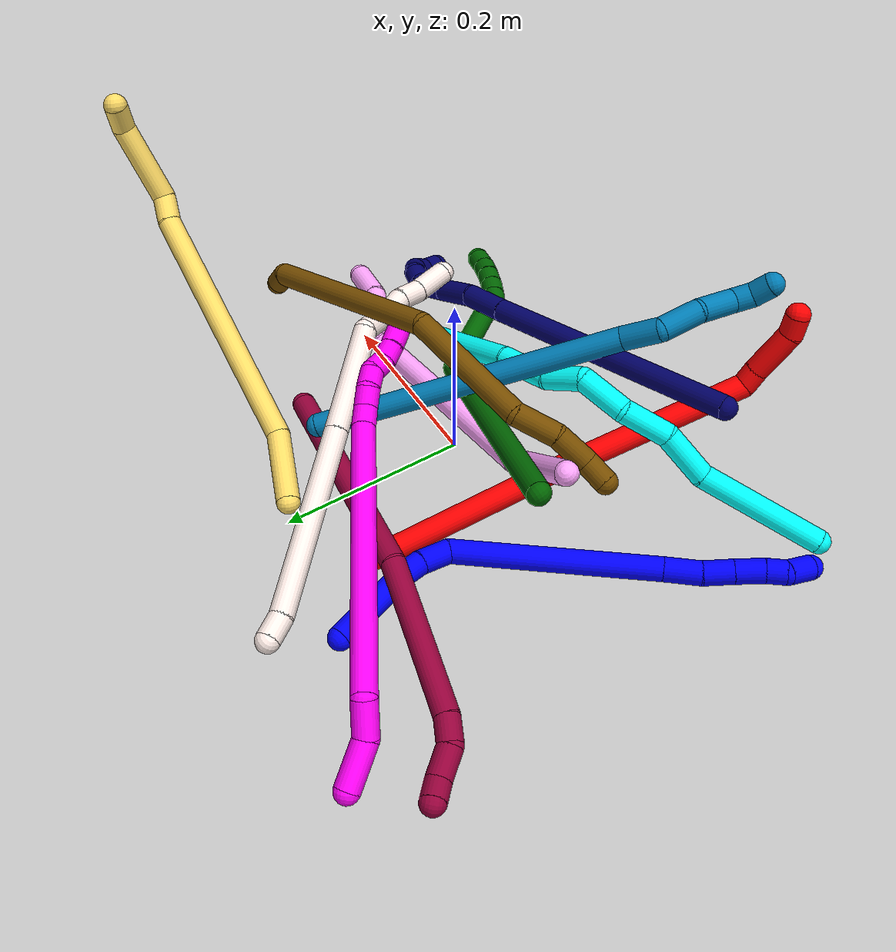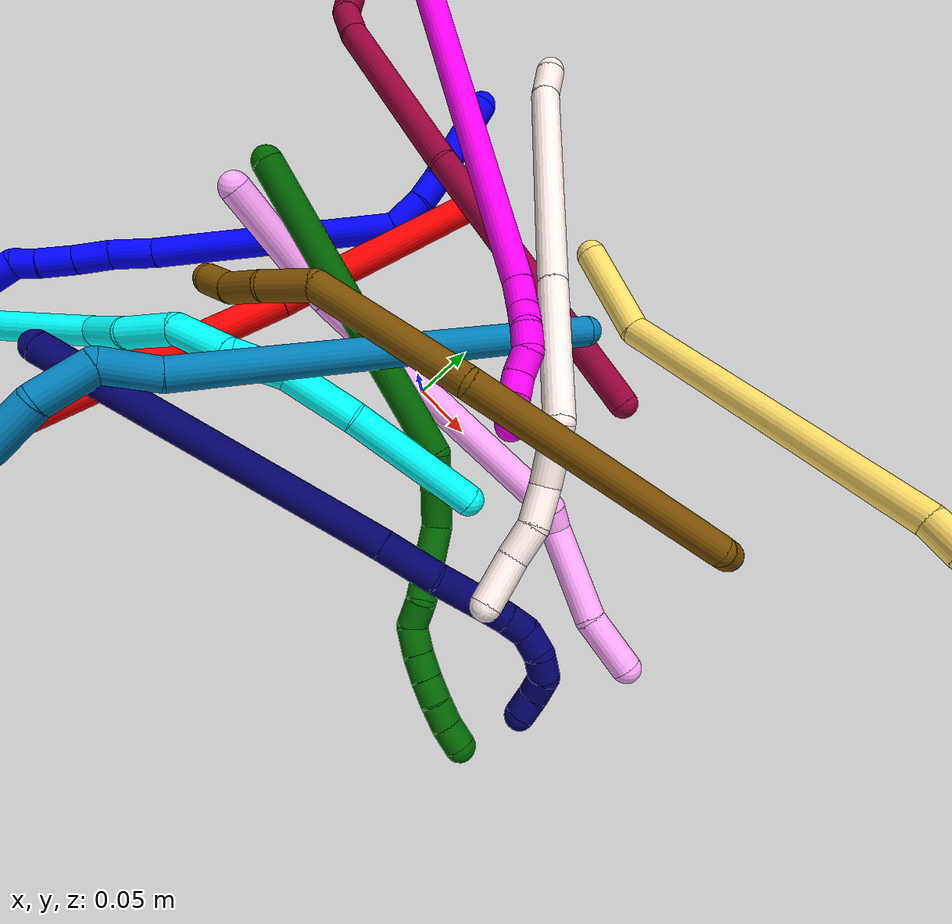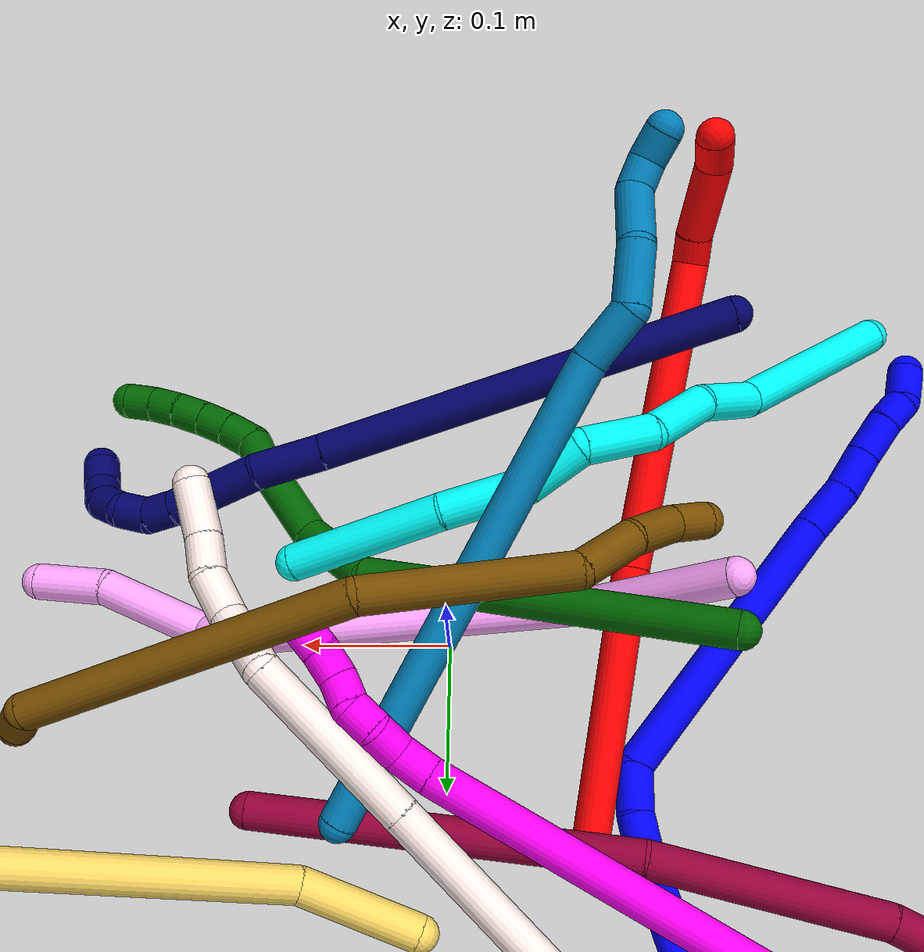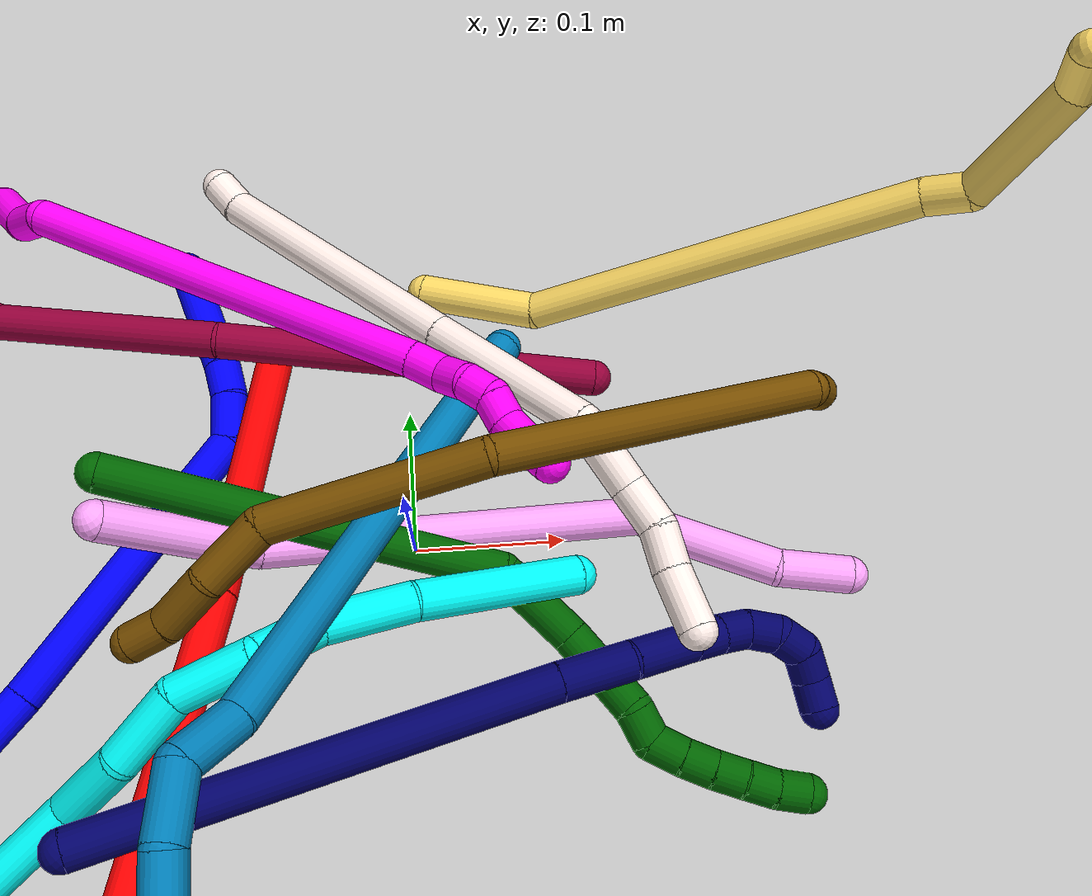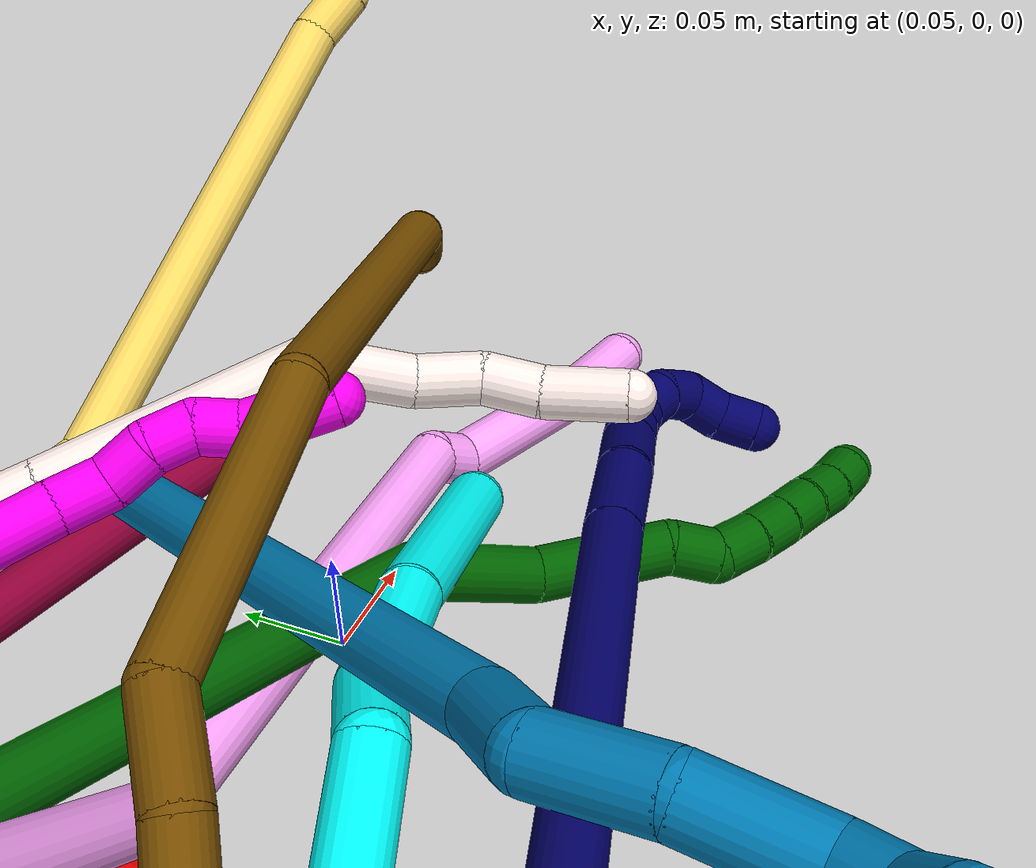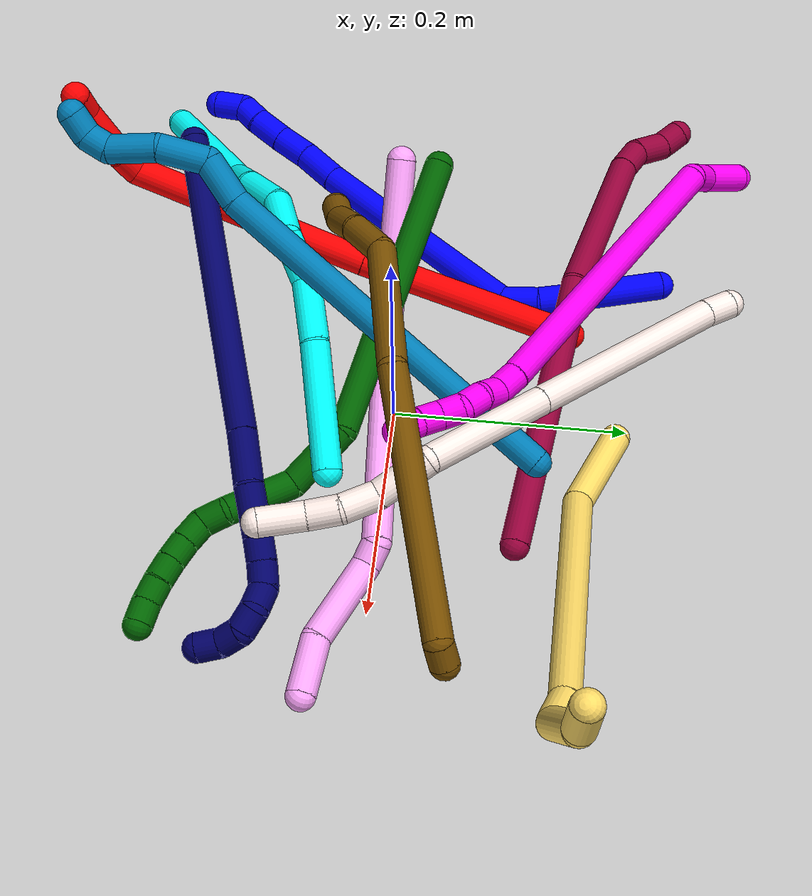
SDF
<sdf version="1.7">
 <world name="default">
  <plugin name="TubeGeneratorPlugin" filename="libtube_generator_plugin.so"/>
  <model name="photoneo_s_sensor">
   <static>1</static>
   <pose>0 0 2 1.57079 1.57079 3.14159</pose>
   <link name="link">
    <inertial><mass>0.1</mass></inertial>
    <sensor name="sensor" type="depth">
     <update_rate>30</update_rate>
     <camera>
      <horizontal_fov>1.22</horizontal_fov>
      <image><width>1920</width><height>1200</height><format>B8G8R8</format></image>
      <clip><near>0.1</near><far>4</far></clip>
      <depth_camera><output>points</output></depth_camera>
     </camera>
     <plugin name="camera_plugin" filename="libgazebo_ros_depth_camera.so">
      <baseline>0.2</baseline>
      <alwaysOn>1</alwaysOn>
      <updateRate>0.0</updateRate>
      <cameraName>camera_ir</cameraName>
      <imageTopicName>/camera/color/image_raw</imageTopicName>
      <cameraInfoTopicName>/camera/color/camera_info</cameraInfoTopicName>
      <depthImageTopicName>/camera/depth/image_raw</depthImageTopicName>
      <depthImageCameraInfoTopicName>/camera/depth/camera_info</depthImageCameraInfoTopicName>
      <pointCloudTopicName>/camera/depth/points</pointCloudTopicName>
      <frameName>fr_optical</frameName>
      <pointCloudCutoff>0.1</pointCloudCutoff>
      <pointCloudCutoffMax>2.0</pointCloudCutoffMax>
      <distortionK1>0</distortionK1>
      <distortionK2>0</distortionK2>
      <distortionK3>0</distortionK3>
      <distortionT1>0</distortionT1>
      <distortionT2>0</distortionT2>
      <CxPrime>0</CxPrime>
      <Cx>0</Cx>
      <Cy>0</Cy>
      <focalLength>0</focalLength>
      <hackBaseline>0</hackBaseline>
     </plugin>
    </sensor>
   </link>
  </model>
  <gravity>0 0 -9.8</gravity>
  <magnetic_field>6e-06 2.3e-05 -4.2e-05</magnetic_field>
  <atmosphere type="adiabatic"/>
  <physics name="default_physics" default="0" type="ode">
   <max_step_size>0.003</max_step_size>
   <real_time_factor>1</real_time_factor>
   <real_time_update_rate>1000</real_time_update_rate>
   <max_contacts>10000</max_contacts>
   <ode>
    <solver>
     <type>quick</type>
     <iters>100</iters>
     <sor>1.3</sor>
     <use_dynamic_moi_rescaling>0</use_dynamic_moi_rescaling>
    </solver>
    <constraints>
     <contact_max_correcting_vel>0</contact_max_correcting_vel>
     <contact_surface_layer>0.001</contact_surface_layer>
     <cfm>0</cfm>
     <erp>0.2</erp>
    </constraints>
   </ode>
  </physics>
  <scene><ambient>0.4 0.4 0.4 1</ambient><background>0.7 0.7 0.7 1</background><shadows>0</shadows></scene>
  <audio><device>default</device></audio>
  <spherical_coordinates>
   <surface_model>EARTH_WGS84</surface_model>
   <latitude_deg>0</latitude_deg>
   <longitude_deg>0</longitude_deg>
   <elevation>0</elevation>
   <heading_deg>0</heading_deg>
  </spherical_coordinates>
  <model name="bin">
   <static>1</static>
   <link name="bottom">
    <collision name="collision-bottom">
     <pose>0 0 -0.01 0 -0 0</pose>
     <geometry><box><size>0.8 0.6 0.02</size></box></geometry>
     <surface>
      <friction><ode><mu>100</mu><mu2>100</mu2></ode></friction>
      <contact><collide_bitmask>65535</collide_bitmask></contact>
     </surface>
    </collision>
   </link>
   <link name="west_wall">
    <collision name="collision-west_wall">
     <pose>-0.41 0 0.1 0 -0 0</pose>
     <geometry><box><size>0.02 0.6 0.2</size></box></geometry>
     <surface>
      <friction><ode><mu>100</mu><mu2>100</mu2></ode></friction>
      <contact><collide_bitmask>65535</collide_bitmask></contact>
     </surface>
    </collision>
   </link>
   <link name="east_wall">
    <collision name="collision-east_wall">
     <pose>0.41 0 0.1 0 -0 0</pose>
     <geometry><box><size>0.02 0.6 0.2</size></box></geometry>
     <surface>
      <friction><ode><mu>100</mu><mu2>100</mu2></ode></friction>
      <contact><collide_bitmask>65535</collide_bitmask></contact>
     </surface>
    </collision>
   </link>
   <link name="south_wall">
    <collision name="collision-south_wall">
     <pose>0 -0.31 0.1 0 -0 0</pose>
     <geometry><box><size>0.8 0.02 0.2</size></box></geometry>
     <surface>
      <friction><ode><mu>100</mu><mu2>100</mu2></ode></friction>
      <contact><collide_bitmask>65535</collide_bitmask></contact>
     </surface>
    </collision>
   </link>
   <link name="north_wall">
    <collision name="collision-north_wall">
     <pose>0 0.31 0.1 0 -0 0</pose>
     <geometry><box><size>0.8 0.02 0.2</size></box></geometry>
     <surface>
      <friction><ode><mu>100</mu><mu2>100</mu2></ode></friction>
      <contact><collide_bitmask>65535</collide_bitmask></contact>
     </surface>
    </collision>
   </link>
  </model>
  <model name="1">
   <static>0</static>
   <link name="1">
    <collision name="collision-cylinder-e_1_1_4">
     <pose>-0.011994 0.00322 0.041708 -0.077057 -0.279239 0.010834</pose>
     <geometry><cylinder><radius>0.0125</radius><length>0.087035</length></cylinder></geometry>
     <surface>
      <friction><ode><mu>1.16</mu><mu2>1.16</mu2><slip1>0</slip1><slip2>0</slip2></ode></friction>
      <contact><ode><kp>1e+06</kp><kd>1</kd><max_vel>0</max_vel><min_depth>0.001</min_depth></ode></contact>
     </surface>
    </collision>
    <visual name="visual-cylinder-e_1_1_4">
     <pose>-0.011994 0.00322 0.041708 -0.077057 -0.279239 0.010834</pose>
     <geometry><cylinder><radius>0.0125</radius><length>0.087035</length></cylinder></geometry>
     <material><ambient>0 0 1 1</ambient></material>
    </visual>
    <collision name="collision-cylinder-e_2_4_5">
     <pose>-0.026558 0.005566 0.095098 0.074744 -0.215849 -0.008102</pose>
     <geometry><cylinder><radius>0.0125</radius><length>0.023987</length></cylinder></geometry>
     <surface>
      <friction><ode><mu>1.16</mu><mu2>1.16</mu2><slip1>0</slip1><slip2>0</slip2></ode></friction>
      <contact><ode><kp>1e+06</kp><kd>1</kd><max_vel>0</max_vel><min_depth>0.001</min_depth></ode></contact>
     </surface>
    </collision>
    <visual name="visual-cylinder-e_2_4_5">
     <pose>-0.026558 0.005566 0.095098 0.074744 -0.215849 -0.008102</pose>
     <geometry><cylinder><radius>0.0125</radius><length>0.023987</length></cylinder></geometry>
     <material><ambient>0 0 1 1</ambient></material>
    </visual>
    <collision name="collision-cylinder-e_3_5_6">
     <pose>-0.032827 -0.000158 0.121903 0.310249 -0.228925 -0.035953</pose>
     <geometry><cylinder><radius>0.0125</radius><length>0.032613</length></cylinder></geometry>
     <surface>
      <friction><ode><mu>1.16</mu><mu2>1.16</mu2><slip1>0</slip1><slip2>0</slip2></ode></friction>
      <contact><ode><kp>1e+06</kp><kd>1</kd><max_vel>0</max_vel><min_depth>0.001</min_depth></ode></contact>
     </surface>
    </collision>
    <visual name="visual-cylinder-e_3_5_6">
     <pose>-0.032827 -0.000158 0.121903 0.310249 -0.228925 -0.035953</pose>
     <geometry><cylinder><radius>0.0125</radius><length>0.032613</length></cylinder></geometry>
     <material><ambient>0 0 1 1</ambient></material>
    </visual>
    <collision name="collision-cylinder-e_4_6_7">
     <pose>-0.081364 -0.08303 0.19201 0.956925 -0.43914 -0.23047</pose>
     <geometry><cylinder><radius>0.0125</radius><length>0.210915</length></cylinder></geometry>
     <surface>
      <friction><ode><mu>1.16</mu><mu2>1.16</mu2><slip1>0</slip1><slip2>0</slip2></ode></friction>
      <contact><ode><kp>1e+06</kp><kd>1</kd><max_vel>0</max_vel><min_depth>0.001</min_depth></ode></contact>
     </surface>
    </collision>
    <visual name="visual-cylinder-e_4_6_7">
     <pose>-0.081364 -0.08303 0.19201 0.956925 -0.43914 -0.23047</pose>
     <geometry><cylinder><radius>0.0125</radius><length>0.210915</length></cylinder></geometry>
     <material><ambient>0 0 1 1</ambient></material>
    </visual>
    <collision name="collision-cylinder-e_5_7_8">
     <pose>-0.134882 -0.175428 0.255885 1.01679 -0.474532 -0.267896</pose>
     <geometry><cylinder><radius>0.0125</radius><length>0.038003</length></cylinder></geometry>
     <surface>
      <friction><ode><mu>1.16</mu><mu2>1.16</mu2><slip1>0</slip1><slip2>0</slip2></ode></friction>
      <contact><ode><kp>1e+06</kp><kd>1</kd><max_vel>0</max_vel><min_depth>0.001</min_depth></ode></contact>
     </surface>
    </collision>
    <visual name="visual-cylinder-e_5_7_8">
     <pose>-0.134882 -0.175428 0.255885 1.01679 -0.474532 -0.267896</pose>
     <geometry><cylinder><radius>0.0125</radius><length>0.038003</length></cylinder></geometry>
     <material><ambient>0 0 1 1</ambient></material>
    </visual>
    <collision name="collision-cylinder-e_6_8_9">
     <pose>-0.15142 -0.199662 0.273566 0.842749 -0.536527 -0.245187</pose>
     <geometry><cylinder><radius>0.0125</radius><length>0.030735</length></cylinder></geometry>
     <surface>
      <friction><ode><mu>1.16</mu><mu2>1.16</mu2><slip1>0</slip1><slip2>0</slip2></ode></friction>
      <contact><ode><kp>1e+06</kp><kd>1</kd><max_vel>0</max_vel><min_depth>0.001</min_depth></ode></contact>
     </surface>
    </collision>
    <visual name="visual-cylinder-e_6_8_9">
     <pose>-0.15142 -0.199662 0.273566 0.842749 -0.536527 -0.245187</pose>
     <geometry><cylinder><radius>0.0125</radius><length>0.030735</length></cylinder></geometry>
     <material><ambient>0 0 1 1</ambient></material>
    </visual>
    <collision name="collision-cylinder-e_7_9_10">
     <pose>-0.167282 -0.219442 0.290336 0.893322 -0.561344 -0.274407</pose>
     <geometry><cylinder><radius>0.0125</radius><length>0.030082</length></cylinder></geometry>
     <surface>
      <friction><ode><mu>1.16</mu><mu2>1.16</mu2><slip1>0</slip1><slip2>0</slip2></ode></friction>
      <contact><ode><kp>1e+06</kp><kd>1</kd><max_vel>0</max_vel><min_depth>0.001</min_depth></ode></contact>
     </surface>
    </collision>
    <visual name="visual-cylinder-e_7_9_10">
     <pose>-0.167282 -0.219442 0.290336 0.893322 -0.561344 -0.274407</pose>
     <geometry><cylinder><radius>0.0125</radius><length>0.030082</length></cylinder></geometry>
     <material><ambient>0 0 1 1</ambient></material>
    </visual>
    <collision name="collision-cylinder-e_8_10_11">
     <pose>-0.180578 -0.23702 0.302802 1.04102 -0.537574 -0.313215</pose>
     <geometry><cylinder><radius>0.0125</radius><length>0.020661</length></cylinder></geometry>
     <surface>
      <friction><ode><mu>1.16</mu><mu2>1.16</mu2><slip1>0</slip1><slip2>0</slip2></ode></friction>
      <contact><ode><kp>1e+06</kp><kd>1</kd><max_vel>0</max_vel><min_depth>0.001</min_depth></ode></contact>
     </surface>
    </collision>
    <visual name="visual-cylinder-e_8_10_11">
     <pose>-0.180578 -0.23702 0.302802 1.04102 -0.537574 -0.313215</pose>
     <geometry><cylinder><radius>0.0125</radius><length>0.020661</length></cylinder></geometry>
     <material><ambient>0 0 1 1</ambient></material>
    </visual>
    <collision name="collision-cylinder-e_9_11_2">
     <pose>-0.189202 -0.250807 0.318236 0.51037 -0.259677 -0.0681</pose>
     <geometry><cylinder><radius>0.0125</radius><length>0.025969</length></cylinder></geometry>
     <surface>
      <friction><ode><mu>1.16</mu><mu2>1.16</mu2><slip1>0</slip1><slip2>0</slip2></ode></friction>
      <contact><ode><kp>1e+06</kp><kd>1</kd><max_vel>0</max_vel><min_depth>0.001</min_depth></ode></contact>
     </surface>
    </collision>
    <visual name="visual-cylinder-e_9_11_2">
     <pose>-0.189202 -0.250807 0.318236 0.51037 -0.259677 -0.0681</pose>
     <geometry><cylinder><radius>0.0125</radius><length>0.025969</length></cylinder></geometry>
     <material><ambient>0 0 1 1</ambient></material>
    </visual>
    <collision name="collision-sphere-2">
     <pose>-0.192536 -0.256938 0.329186 0 -0 0</pose>
     <geometry><sphere><radius>0.0125</radius></sphere></geometry>
     <surface>
      <friction><ode><mu>1.16</mu><mu2>1.16</mu2><slip1>0</slip1><slip2>0</slip2></ode></friction>
      <contact><ode><kp>1e+06</kp><kd>1</kd><max_vel>0</max_vel><min_depth>0.001</min_depth></ode></contact>
     </surface>
    </collision>
    <visual name="visual-sphere-2">
     <pose>-0.192536 -0.256938 0.329186 0 -0 0</pose>
     <geometry><sphere><radius>0.0125</radius></sphere></geometry>
     <material><ambient>0 0 1 1</ambient></material>
    </visual>
    <collision name="collision-sphere-11">
     <pose>-0.185868 -0.244677 0.307286 0 -0 0</pose>
     <geometry><sphere><radius>0.0125</radius></sphere></geometry>
     <surface>
      <friction><ode><mu>1.16</mu><mu2>1.16</mu2><slip1>0</slip1><slip2>0</slip2></ode></friction>
      <contact><ode><kp>1e+06</kp><kd>1</kd><max_vel>0</max_vel><min_depth>0.001</min_depth></ode></contact>
     </surface>
    </collision>
    <visual name="visual-sphere-11">
     <pose>-0.185868 -0.244677 0.307286 0 -0 0</pose>
     <geometry><sphere><radius>0.0125</radius></sphere></geometry>
     <material><ambient>0 0 1 1</ambient></material>
    </visual>
    <collision name="collision-sphere-10">
     <pose>-0.175288 -0.229363 0.298318 0 -0 0</pose>
     <geometry><sphere><radius>0.0125</radius></sphere></geometry>
     <surface>
      <friction><ode><mu>1.16</mu><mu2>1.16</mu2><slip1>0</slip1><slip2>0</slip2></ode></friction>
      <contact><ode><kp>1e+06</kp><kd>1</kd><max_vel>0</max_vel><min_depth>0.001</min_depth></ode></contact>
     </surface>
    </collision>
    <visual name="visual-sphere-10">
     <pose>-0.175288 -0.229363 0.298318 0 -0 0</pose>
     <geometry><sphere><radius>0.0125</radius></sphere></geometry>
     <material><ambient>0 0 1 1</ambient></material>
    </visual>
    <collision name="collision-sphere-9">
     <pose>-0.159275 -0.209521 0.282355 0 -0 0</pose>
     <geometry><sphere><radius>0.0125</radius></sphere></geometry>
     <surface>
      <friction><ode><mu>1.16</mu><mu2>1.16</mu2><slip1>0</slip1><slip2>0</slip2></ode></friction>
      <contact><ode><kp>1e+06</kp><kd>1</kd><max_vel>0</max_vel><min_depth>0.001</min_depth></ode></contact>
     </surface>
    </collision>
    <visual name="visual-sphere-9">
     <pose>-0.159275 -0.209521 0.282355 0 -0 0</pose>
     <geometry><sphere><radius>0.0125</radius></sphere></geometry>
     <material><ambient>0 0 1 1</ambient></material>
    </visual>
    <collision name="collision-sphere-4">
     <pose>-0.023989 0.006441 0.083416 0 -0 0</pose>
     <geometry><sphere><radius>0.0125</radius></sphere></geometry>
     <surface>
      <friction><ode><mu>1.16</mu><mu2>1.16</mu2><slip1>0</slip1><slip2>0</slip2></ode></friction>
      <contact><ode><kp>1e+06</kp><kd>1</kd><max_vel>0</max_vel><min_depth>0.001</min_depth></ode></contact>
     </surface>
    </collision>
    <visual name="visual-sphere-4">
     <pose>-0.023989 0.006441 0.083416 0 -0 0</pose>
     <geometry><sphere><radius>0.0125</radius></sphere></geometry>
     <material><ambient>0 0 1 1</ambient></material>
    </visual>
    <collision name="collision-sphere-1">
     <geometry><sphere><radius>0.0125</radius></sphere></geometry>
     <surface>
      <friction><ode><mu>1.16</mu><mu2>1.16</mu2><slip1>0</slip1><slip2>0</slip2></ode></friction>
      <contact><ode><kp>1e+06</kp><kd>1</kd><max_vel>0</max_vel><min_depth>0.001</min_depth></ode></contact>
     </surface>
    </collision>
    <visual name="visual-sphere-1">
     <geometry><sphere><radius>0.0125</radius></sphere></geometry>
     <material><ambient>0 0 1 1</ambient></material>
    </visual>
    <collision name="collision-sphere-8">
     <pose>-0.143565 -0.189802 0.264777 0 -0 0</pose>
     <geometry><sphere><radius>0.0125</radius></sphere></geometry>
     <surface>
      <friction><ode><mu>1.16</mu><mu2>1.16</mu2><slip1>0</slip1><slip2>0</slip2></ode></friction>
      <contact><ode><kp>1e+06</kp><kd>1</kd><max_vel>0</max_vel><min_depth>0.001</min_depth></ode></contact>
     </surface>
    </collision>
    <visual name="visual-sphere-8">
     <pose>-0.143565 -0.189802 0.264777 0 -0 0</pose>
     <geometry><sphere><radius>0.0125</radius></sphere></geometry>
     <material><ambient>0 0 1 1</ambient></material>
    </visual>
    <collision name="collision-sphere-5">
     <pose>-0.029126 0.004691 0.10678 0 -0 0</pose>
     <geometry><sphere><radius>0.0125</radius></sphere></geometry>
     <surface>
      <friction><ode><mu>1.16</mu><mu2>1.16</mu2><slip1>0</slip1><slip2>0</slip2></ode></friction>
      <contact><ode><kp>1e+06</kp><kd>1</kd><max_vel>0</max_vel><min_depth>0.001</min_depth></ode></contact>
     </surface>
    </collision>
    <visual name="visual-sphere-5">
     <pose>-0.029126 0.004691 0.10678 0 -0 0</pose>
     <geometry><sphere><radius>0.0125</radius></sphere></geometry>
     <material><ambient>0 0 1 1</ambient></material>
    </visual>
    <collision name="collision-sphere-6">
     <pose>-0.036527 -0.005006 0.137026 0 -0 0</pose>
     <geometry><sphere><radius>0.0125</radius></sphere></geometry>
     <surface>
      <friction><ode><mu>1.16</mu><mu2>1.16</mu2><slip1>0</slip1><slip2>0</slip2></ode></friction>
      <contact><ode><kp>1e+06</kp><kd>1</kd><max_vel>0</max_vel><min_depth>0.001</min_depth></ode></contact>
     </surface>
    </collision>
    <visual name="visual-sphere-6">
     <pose>-0.036527 -0.005006 0.137026 0 -0 0</pose>
     <geometry><sphere><radius>0.0125</radius></sphere></geometry>
     <material><ambient>0 0 1 1</ambient></material>
    </visual>
    <collision name="collision-sphere-7">
     <pose>-0.1262 -0.161055 0.246993 0 -0 0</pose>
     <geometry><sphere><radius>0.0125</radius></sphere></geometry>
     <surface>
      <friction><ode><mu>1.16</mu><mu2>1.16</mu2><slip1>0</slip1><slip2>0</slip2></ode></friction>
      <contact><ode><kp>1e+06</kp><kd>1</kd><max_vel>0</max_vel><min_depth>0.001</min_depth></ode></contact>
     </surface>
    </collision>
    <visual name="visual-sphere-7">
     <pose>-0.1262 -0.161055 0.246993 0 -0 0</pose>
     <geometry><sphere><radius>0.0125</radius></sphere></geometry>
     <material><ambient>0 0 1 1</ambient></material>
    </visual>
    <inertial>
     <pose>-0.086737 -0.095837 0.183543 0 -0 0</pose>
     <mass>0.5</mass>
     <inertia>
      <ixx>0.000592</ixx>
      <ixy>0</ixy>
      <ixz>0</ixz>
      <iyy>0.000395</iyy>
      <iyz>0</iyz>
      <izz>0.00098</izz>
     </inertia>
    </inertial>
   </link>
   <pose>-0.155466 0.221519 0.012494 2.12774 1.12628 0.865992</pose>
  </model>
  <model name="2">
   <static>0</static>
   <link name="2">
    <collision name="collision-cylinder-e_1_1_4">
     <pose>-0.010994 -0.058014 0.076432 0.64925 -0.11408 -0.038428</pose>
     <geometry><cylinder><radius>0.0125</radius><length>0.193167</length></cylinder></geometry>
     <surface>
      <friction><ode><mu>1.16</mu><mu2>1.16</mu2><slip1>0</slip1><slip2>0</slip2></ode></friction>
      <contact><ode><kp>1e+06</kp><kd>1</kd><max_vel>0</max_vel><min_depth>0.001</min_depth></ode></contact>
     </surface>
    </collision>
    <visual name="visual-cylinder-e_1_1_4">
     <pose>-0.010994 -0.058014 0.076432 0.64925 -0.11408 -0.038428</pose>
     <geometry><cylinder><radius>0.0125</radius><length>0.193167</length></cylinder></geometry>
     <material><ambient>1 0 0 1</ambient></material>
    </visual>
    <collision name="collision-cylinder-e_2_4_5">
     <pose>-0.030759 -0.177487 0.239595 0.616489 -0.082322 -0.026224</pose>
     <geometry><cylinder><radius>0.0125</radius><length>0.21332</length></cylinder></geometry>
     <surface>
      <friction><ode><mu>1.16</mu><mu2>1.16</mu2><slip1>0</slip1><slip2>0</slip2></ode></friction>
      <contact><ode><kp>1e+06</kp><kd>1</kd><max_vel>0</max_vel><min_depth>0.001</min_depth></ode></contact>
     </surface>
    </collision>
    <visual name="visual-cylinder-e_2_4_5">
     <pose>-0.030759 -0.177487 0.239595 0.616489 -0.082322 -0.026224</pose>
     <geometry><cylinder><radius>0.0125</radius><length>0.21332</length></cylinder></geometry>
     <material><ambient>1 0 0 1</ambient></material>
    </visual>
    <collision name="collision-cylinder-e_3_5_6">
     <pose>-0.034971 -0.247125 0.330565 1.09258 0.459536 0.282532</pose>
     <geometry><cylinder><radius>0.0125</radius><length>0.020559</length></cylinder></geometry>
     <surface>
      <friction><ode><mu>1.16</mu><mu2>1.16</mu2><slip1>0</slip1><slip2>0</slip2></ode></friction>
      <contact><ode><kp>1e+06</kp><kd>1</kd><max_vel>0</max_vel><min_depth>0.001</min_depth></ode></contact>
     </surface>
    </collision>
    <visual name="visual-cylinder-e_3_5_6">
     <pose>-0.034971 -0.247125 0.330565 1.09258 0.459536 0.282532</pose>
     <geometry><cylinder><radius>0.0125</radius><length>0.020559</length></cylinder></geometry>
     <material><ambient>1 0 0 1</ambient></material>
    </visual>
    <collision name="collision-cylinder-e_4_6_7">
     <pose>-0.016832 -0.273258 0.346181 1.006 0.568554 0.318801</pose>
     <geometry><cylinder><radius>0.0125</radius><length>0.050442</length></cylinder></geometry>
     <surface>
      <friction><ode><mu>1.16</mu><mu2>1.16</mu2><slip1>0</slip1><slip2>0</slip2></ode></friction>
      <contact><ode><kp>1e+06</kp><kd>1</kd><max_vel>0</max_vel><min_depth>0.001</min_depth></ode></contact>
     </surface>
    </collision>
    <visual name="visual-cylinder-e_4_6_7">
     <pose>-0.016832 -0.273258 0.346181 1.006 0.568554 0.318801</pose>
     <geometry><cylinder><radius>0.0125</radius><length>0.050442</length></cylinder></geometry>
     <material><ambient>1 0 0 1</ambient></material>
    </visual>
    <collision name="collision-cylinder-e_5_7_2">
     <pose>0.003783 -0.299963 0.358326 1.48317 0.675148 0.622169</pose>
     <geometry><cylinder><radius>0.0125</radius><length>0.022512</length></cylinder></geometry>
     <surface>
      <friction><ode><mu>1.16</mu><mu2>1.16</mu2><slip1>0</slip1><slip2>0</slip2></ode></friction>
      <contact><ode><kp>1e+06</kp><kd>1</kd><max_vel>0</max_vel><min_depth>0.001</min_depth></ode></contact>
     </surface>
    </collision>
    <visual name="visual-cylinder-e_5_7_2">
     <pose>0.003783 -0.299963 0.358326 1.48317 0.675148 0.622169</pose>
     <geometry><cylinder><radius>0.0125</radius><length>0.022512</length></cylinder></geometry>
     <material><ambient>1 0 0 1</ambient></material>
    </visual>
    <collision name="collision-sphere-2">
     <pose>0.010818 -0.308716 0.359095 0 -0 0</pose>
     <geometry><sphere><radius>0.0125</radius></sphere></geometry>
     <surface>
      <friction><ode><mu>1.16</mu><mu2>1.16</mu2><slip1>0</slip1><slip2>0</slip2></ode></friction>
      <contact><ode><kp>1e+06</kp><kd>1</kd><max_vel>0</max_vel><min_depth>0.001</min_depth></ode></contact>
     </surface>
    </collision>
    <visual name="visual-sphere-2">
     <pose>0.010818 -0.308716 0.359095 0 -0 0</pose>
     <geometry><sphere><radius>0.0125</radius></sphere></geometry>
     <material><ambient>1 0 0 1</ambient></material>
    </visual>
    <collision name="collision-sphere-7">
     <pose>-0.003252 -0.29121 0.357557 0 -0 0</pose>
     <geometry><sphere><radius>0.0125</radius></sphere></geometry>
     <surface>
      <friction><ode><mu>1.16</mu><mu2>1.16</mu2><slip1>0</slip1><slip2>0</slip2></ode></friction>
      <contact><ode><kp>1e+06</kp><kd>1</kd><max_vel>0</max_vel><min_depth>0.001</min_depth></ode></contact>
     </surface>
    </collision>
    <visual name="visual-sphere-7">
     <pose>-0.003252 -0.29121 0.357557 0 -0 0</pose>
     <geometry><sphere><radius>0.0125</radius></sphere></geometry>
     <material><ambient>1 0 0 1</ambient></material>
    </visual>
    <collision name="collision-sphere-6">
     <pose>-0.030411 -0.255305 0.334805 0 -0 0</pose>
     <geometry><sphere><radius>0.0125</radius></sphere></geometry>
     <surface>
      <friction><ode><mu>1.16</mu><mu2>1.16</mu2><slip1>0</slip1><slip2>0</slip2></ode></friction>
      <contact><ode><kp>1e+06</kp><kd>1</kd><max_vel>0</max_vel><min_depth>0.001</min_depth></ode></contact>
     </surface>
    </collision>
    <visual name="visual-sphere-6">
     <pose>-0.030411 -0.255305 0.334805 0 -0 0</pose>
     <geometry><sphere><radius>0.0125</radius></sphere></geometry>
     <material><ambient>1 0 0 1</ambient></material>
    </visual>
    <collision name="collision-sphere-5">
     <pose>-0.03953 -0.238946 0.326325 0 -0 0</pose>
     <geometry><sphere><radius>0.0125</radius></sphere></geometry>
     <surface>
      <friction><ode><mu>1.16</mu><mu2>1.16</mu2><slip1>0</slip1><slip2>0</slip2></ode></friction>
      <contact><ode><kp>1e+06</kp><kd>1</kd><max_vel>0</max_vel><min_depth>0.001</min_depth></ode></contact>
     </surface>
    </collision>
    <visual name="visual-sphere-5">
     <pose>-0.03953 -0.238946 0.326325 0 -0 0</pose>
     <geometry><sphere><radius>0.0125</radius></sphere></geometry>
     <material><ambient>1 0 0 1</ambient></material>
    </visual>
    <collision name="collision-sphere-1">
     <geometry><sphere><radius>0.0125</radius></sphere></geometry>
     <surface>
      <friction><ode><mu>1.16</mu><mu2>1.16</mu2><slip1>0</slip1><slip2>0</slip2></ode></friction>
      <contact><ode><kp>1e+06</kp><kd>1</kd><max_vel>0</max_vel><min_depth>0.001</min_depth></ode></contact>
     </surface>
    </collision>
    <visual name="visual-sphere-1">
     <geometry><sphere><radius>0.0125</radius></sphere></geometry>
     <material><ambient>1 0 0 1</ambient></material>
    </visual>
    <collision name="collision-sphere-4">
     <pose>-0.021989 -0.116027 0.152865 0 -0 0</pose>
     <geometry><sphere><radius>0.0125</radius></sphere></geometry>
     <surface>
      <friction><ode><mu>1.16</mu><mu2>1.16</mu2><slip1>0</slip1><slip2>0</slip2></ode></friction>
      <contact><ode><kp>1e+06</kp><kd>1</kd><max_vel>0</max_vel><min_depth>0.001</min_depth></ode></contact>
     </surface>
    </collision>
    <visual name="visual-sphere-4">
     <pose>-0.021989 -0.116027 0.152865 0 -0 0</pose>
     <geometry><sphere><radius>0.0125</radius></sphere></geometry>
     <material><ambient>1 0 0 1</ambient></material>
    </visual>
    <inertial>
     <pose>-0.020336 -0.14937 0.196399 0 -0 0</pose>
     <mass>0.5</mass>
     <inertia>
      <ixx>0.001391</ixx>
      <ixy>0</ixy>
      <ixz>0</ixz>
      <iyy>0.001099</iyy>
      <iyz>0</iyz>
      <izz>0.001004</izz>
     </inertia>
    </inertial>
   </link>
   <pose>-0.092126 0.145712 0.011469 -1.66633 -0.92538 2.46548</pose>
  </model>
  <model name="3">
   <static>0</static>
   <link name="3">
    <collision name="collision-cylinder-e_1_1_4">
     <pose>0.064072 0.015549 0.010611 -0.971942 1.28504 -0.752996</pose>
     <geometry><cylinder><radius>0.0125</radius><length>0.13356</length></cylinder></geometry>
     <surface>
      <friction><ode><mu>1.16</mu><mu2>1.16</mu2><slip1>0</slip1><slip2>0</slip2></ode></friction>
      <contact><ode><kp>1e+06</kp><kd>1</kd><max_vel>0</max_vel><min_depth>0.001</min_depth></ode></contact>
     </surface>
    </collision>
    <visual name="visual-cylinder-e_1_1_4">
     <pose>0.064072 0.015549 0.010611 -0.971942 1.28504 -0.752996</pose>
     <geometry><cylinder><radius>0.0125</radius><length>0.13356</length></cylinder></geometry>
     <material><ambient>0.003922 1 0.996078 1</ambient></material>
    </visual>
    <collision name="collision-cylinder-e_2_4_5">
     <pose>0.150495 0.046999 0.024985 -1.33848 0.939498 -0.7637</pose>
     <geometry><cylinder><radius>0.0125</radius><length>0.055376</length></cylinder></geometry>
     <surface>
      <friction><ode><mu>1.16</mu><mu2>1.16</mu2><slip1>0</slip1><slip2>0</slip2></ode></friction>
      <contact><ode><kp>1e+06</kp><kd>1</kd><max_vel>0</max_vel><min_depth>0.001</min_depth></ode></contact>
     </surface>
    </collision>
    <visual name="visual-cylinder-e_2_4_5">
     <pose>0.150495 0.046999 0.024985 -1.33848 0.939498 -0.7637</pose>
     <geometry><cylinder><radius>0.0125</radius><length>0.055376</length></cylinder></geometry>
     <material><ambient>0.003922 1 0.996078 1</ambient></material>
    </visual>
    <collision name="collision-cylinder-e_3_5_6">
     <pose>0.197225 0.069926 0.030225 -1.36341 1.28442 -1.09108</pose>
     <geometry><cylinder><radius>0.0125</radius><length>0.050827</length></cylinder></geometry>
     <surface>
      <friction><ode><mu>1.16</mu><mu2>1.16</mu2><slip1>0</slip1><slip2>0</slip2></ode></friction>
      <contact><ode><kp>1e+06</kp><kd>1</kd><max_vel>0</max_vel><min_depth>0.001</min_depth></ode></contact>
     </surface>
    </collision>
    <visual name="visual-cylinder-e_3_5_6">
     <pose>0.197225 0.069926 0.030225 -1.36341 1.28442 -1.09108</pose>
     <geometry><cylinder><radius>0.0125</radius><length>0.050827</length></cylinder></geometry>
     <material><ambient>0.003922 1 0.996078 1</ambient></material>
    </visual>
    <collision name="collision-cylinder-e_4_6_7">
     <pose>0.243614 0.082879 0.043072 -0.480654 1.04332 -0.279869</pose>
     <geometry><cylinder><radius>0.0125</radius><length>0.050943</length></cylinder></geometry>
     <surface>
      <friction><ode><mu>1.16</mu><mu2>1.16</mu2><slip1>0</slip1><slip2>0</slip2></ode></friction>
      <contact><ode><kp>1e+06</kp><kd>1</kd><max_vel>0</max_vel><min_depth>0.001</min_depth></ode></contact>
     </surface>
    </collision>
    <visual name="visual-cylinder-e_4_6_7">
     <pose>0.243614 0.082879 0.043072 -0.480654 1.04332 -0.279869</pose>
     <geometry><cylinder><radius>0.0125</radius><length>0.050943</length></cylinder></geometry>
     <material><ambient>0.003922 1 0.996078 1</ambient></material>
    </visual>
    <collision name="collision-cylinder-e_5_7_8">
     <pose>0.282528 0.079729 0.063444 0.789468 0.923239 0.408704</pose>
     <geometry><cylinder><radius>0.0125</radius><length>0.042391</length></cylinder></geometry>
     <surface>
      <friction><ode><mu>1.16</mu><mu2>1.16</mu2><slip1>0</slip1><slip2>0</slip2></ode></friction>
      <contact><ode><kp>1e+06</kp><kd>1</kd><max_vel>0</max_vel><min_depth>0.001</min_depth></ode></contact>
     </surface>
    </collision>
    <visual name="visual-cylinder-e_5_7_8">
     <pose>0.282528 0.079729 0.063444 0.789468 0.923239 0.408704</pose>
     <geometry><cylinder><radius>0.0125</radius><length>0.042391</length></cylinder></geometry>
     <material><ambient>0.003922 1 0.996078 1</ambient></material>
    </visual>
    <collision name="collision-cylinder-e_6_8_9">
     <pose>0.321437 0.066251 0.090669 0.23699 0.865226 0.109843</pose>
     <geometry><cylinder><radius>0.0125</radius><length>0.057811</length></cylinder></geometry>
     <surface>
      <friction><ode><mu>1.16</mu><mu2>1.16</mu2><slip1>0</slip1><slip2>0</slip2></ode></friction>
      <contact><ode><kp>1e+06</kp><kd>1</kd><max_vel>0</max_vel><min_depth>0.001</min_depth></ode></contact>
     </surface>
    </collision>
    <visual name="visual-cylinder-e_6_8_9">
     <pose>0.321437 0.066251 0.090669 0.23699 0.865226 0.109843</pose>
     <geometry><cylinder><radius>0.0125</radius><length>0.057811</length></cylinder></geometry>
     <material><ambient>0.003922 1 0.996078 1</ambient></material>
    </visual>
    <collision name="collision-cylinder-e_7_9_2">
     <pose>0.380244 0.044984 0.145445 0.432295 0.740587 0.17007</pose>
     <geometry><cylinder><radius>0.0125</radius><length>0.109091</length></cylinder></geometry>
     <surface>
      <friction><ode><mu>1.16</mu><mu2>1.16</mu2><slip1>0</slip1><slip2>0</slip2></ode></friction>
      <contact><ode><kp>1e+06</kp><kd>1</kd><max_vel>0</max_vel><min_depth>0.001</min_depth></ode></contact>
     </surface>
    </collision>
    <visual name="visual-cylinder-e_7_9_2">
     <pose>0.380244 0.044984 0.145445 0.432295 0.740587 0.17007</pose>
     <geometry><cylinder><radius>0.0125</radius><length>0.109091</length></cylinder></geometry>
     <material><ambient>0.003922 1 0.996078 1</ambient></material>
    </visual>
    <collision name="collision-sphere-2">
     <pose>0.417047 0.028117 0.182 0 -0 0</pose>
     <geometry><sphere><radius>0.0125</radius></sphere></geometry>
     <surface>
      <friction><ode><mu>1.16</mu><mu2>1.16</mu2><slip1>0</slip1><slip2>0</slip2></ode></friction>
      <contact><ode><kp>1e+06</kp><kd>1</kd><max_vel>0</max_vel><min_depth>0.001</min_depth></ode></contact>
     </surface>
    </collision>
    <visual name="visual-sphere-2">
     <pose>0.417047 0.028117 0.182 0 -0 0</pose>
     <geometry><sphere><radius>0.0125</radius></sphere></geometry>
     <material><ambient>0.003922 1 0.996078 1</ambient></material>
    </visual>
    <collision name="collision-sphere-9">
     <pose>0.343441 0.06185 0.10889 0 -0 0</pose>
     <geometry><sphere><radius>0.0125</radius></sphere></geometry>
     <surface>
      <friction><ode><mu>1.16</mu><mu2>1.16</mu2><slip1>0</slip1><slip2>0</slip2></ode></friction>
      <contact><ode><kp>1e+06</kp><kd>1</kd><max_vel>0</max_vel><min_depth>0.001</min_depth></ode></contact>
     </surface>
    </collision>
    <visual name="visual-sphere-9">
     <pose>0.343441 0.06185 0.10889 0 -0 0</pose>
     <geometry><sphere><radius>0.0125</radius></sphere></geometry>
     <material><ambient>0.003922 1 0.996078 1</ambient></material>
    </visual>
    <collision name="collision-sphere-4">
     <pose>0.128144 0.031097 0.021222 0 -0 0</pose>
     <geometry><sphere><radius>0.0125</radius></sphere></geometry>
     <surface>
      <friction><ode><mu>1.16</mu><mu2>1.16</mu2><slip1>0</slip1><slip2>0</slip2></ode></friction>
      <contact><ode><kp>1e+06</kp><kd>1</kd><max_vel>0</max_vel><min_depth>0.001</min_depth></ode></contact>
     </surface>
    </collision>
    <visual name="visual-sphere-4">
     <pose>0.128144 0.031097 0.021222 0 -0 0</pose>
     <geometry><sphere><radius>0.0125</radius></sphere></geometry>
     <material><ambient>0.003922 1 0.996078 1</ambient></material>
    </visual>
    <collision name="collision-sphere-1">
     <geometry><sphere><radius>0.0125</radius></sphere></geometry>
     <surface>
      <friction><ode><mu>1.16</mu><mu2>1.16</mu2><slip1>0</slip1><slip2>0</slip2></ode></friction>
      <contact><ode><kp>1e+06</kp><kd>1</kd><max_vel>0</max_vel><min_depth>0.001</min_depth></ode></contact>
     </surface>
    </collision>
    <visual name="visual-sphere-1">
     <geometry><sphere><radius>0.0125</radius></sphere></geometry>
     <material><ambient>0.003922 1 0.996078 1</ambient></material>
    </visual>
    <collision name="collision-sphere-8">
     <pose>0.299432 0.070652 0.072449 0 -0 0</pose>
     <geometry><sphere><radius>0.0125</radius></sphere></geometry>
     <surface>
      <friction><ode><mu>1.16</mu><mu2>1.16</mu2><slip1>0</slip1><slip2>0</slip2></ode></friction>
      <contact><ode><kp>1e+06</kp><kd>1</kd><max_vel>0</max_vel><min_depth>0.001</min_depth></ode></contact>
     </surface>
    </collision>
    <visual name="visual-sphere-8">
     <pose>0.299432 0.070652 0.072449 0 -0 0</pose>
     <geometry><sphere><radius>0.0125</radius></sphere></geometry>
     <material><ambient>0.003922 1 0.996078 1</ambient></material>
    </visual>
    <collision name="collision-sphere-5">
     <pose>0.172847 0.062902 0.028747 0 -0 0</pose>
     <geometry><sphere><radius>0.0125</radius></sphere></geometry>
     <surface>
      <friction><ode><mu>1.16</mu><mu2>1.16</mu2><slip1>0</slip1><slip2>0</slip2></ode></friction>
      <contact><ode><kp>1e+06</kp><kd>1</kd><max_vel>0</max_vel><min_depth>0.001</min_depth></ode></contact>
     </surface>
    </collision>
    <visual name="visual-sphere-5">
     <pose>0.172847 0.062902 0.028747 0 -0 0</pose>
     <geometry><sphere><radius>0.0125</radius></sphere></geometry>
     <material><ambient>0.003922 1 0.996078 1</ambient></material>
    </visual>
    <collision name="collision-sphere-6">
     <pose>0.221604 0.076951 0.031703 0 -0 0</pose>
     <geometry><sphere><radius>0.0125</radius></sphere></geometry>
     <surface>
      <friction><ode><mu>1.16</mu><mu2>1.16</mu2><slip1>0</slip1><slip2>0</slip2></ode></friction>
      <contact><ode><kp>1e+06</kp><kd>1</kd><max_vel>0</max_vel><min_depth>0.001</min_depth></ode></contact>
     </surface>
    </collision>
    <visual name="visual-sphere-6">
     <pose>0.221604 0.076951 0.031703 0 -0 0</pose>
     <geometry><sphere><radius>0.0125</radius></sphere></geometry>
     <material><ambient>0.003922 1 0.996078 1</ambient></material>
    </visual>
    <collision name="collision-sphere-7">
     <pose>0.265623 0.088807 0.05444 0 -0 0</pose>
     <geometry><sphere><radius>0.0125</radius></sphere></geometry>
     <surface>
      <friction><ode><mu>1.16</mu><mu2>1.16</mu2><slip1>0</slip1><slip2>0</slip2></ode></friction>
      <contact><ode><kp>1e+06</kp><kd>1</kd><max_vel>0</max_vel><min_depth>0.001</min_depth></ode></contact>
     </surface>
    </collision>
    <visual name="visual-sphere-7">
     <pose>0.265623 0.088807 0.05444 0 -0 0</pose>
     <geometry><sphere><radius>0.0125</radius></sphere></geometry>
     <material><ambient>0.003922 1 0.996078 1</ambient></material>
    </visual>
    <inertial>
     <pose>0.222734 0.049146 0.060658 0 -0 0</pose>
     <mass>0.5</mass>
     <inertia>
      <ixx>0.000154</ixx>
      <ixy>0</ixy>
      <ixz>0</ixz>
      <iyy>0.00033</iyy>
      <iyz>0</iyz>
      <izz>-0.000337</izz>
     </inertia>
    </inertial>
   </link>
   <pose>-0.307175 -0.236976 0.0115 1.86202 -0.16621 0.856982</pose>
  </model>
  <model name="4">
   <static>0</static>
   <link name="4">
    <collision name="collision-cylinder-e_1_1_4">
     <pose>0.031551 -0.006868 0.042739 0.159323 0.629833 0.051999</pose>
     <geometry><cylinder><radius>0.0125</radius><length>0.107131</length></cylinder></geometry>
     <surface>
      <friction><ode><mu>1.16</mu><mu2>1.16</mu2><slip1>0</slip1><slip2>0</slip2></ode></friction>
      <contact><ode><kp>1e+06</kp><kd>1</kd><max_vel>0</max_vel><min_depth>0.001</min_depth></ode></contact>
     </surface>
    </collision>
    <visual name="visual-cylinder-e_1_1_4">
     <pose>0.031551 -0.006868 0.042739 0.159323 0.629833 0.051999</pose>
     <geometry><cylinder><radius>0.0125</radius><length>0.107131</length></cylinder></geometry>
     <material><ambient>1 0.65098 0.996078 1</ambient></material>
    </visual>
    <collision name="collision-cylinder-e_2_4_5">
     <pose>0.17587 -0.006479 0.134181 -0.147898 1.1591 -0.096904</pose>
     <geometry><cylinder><radius>0.0125</radius><length>0.246101</length></cylinder></geometry>
     <surface>
      <friction><ode><mu>1.16</mu><mu2>1.16</mu2><slip1>0</slip1><slip2>0</slip2></ode></friction>
      <contact><ode><kp>1e+06</kp><kd>1</kd><max_vel>0</max_vel><min_depth>0.001</min_depth></ode></contact>
     </surface>
    </collision>
    <visual name="visual-cylinder-e_2_4_5">
     <pose>0.17587 -0.006479 0.134181 -0.147898 1.1591 -0.096904</pose>
     <geometry><cylinder><radius>0.0125</radius><length>0.246101</length></cylinder></geometry>
     <material><ambient>1 0.65098 0.996078 1</ambient></material>
    </visual>
    <collision name="collision-cylinder-e_3_5_6">
     <pose>0.293516 0.00282 0.191477 -0.233365 0.504453 -0.060398</pose>
     <geometry><cylinder><radius>0.0125</radius><length>0.020179</length></cylinder></geometry>
     <surface>
      <friction><ode><mu>1.16</mu><mu2>1.16</mu2><slip1>0</slip1><slip2>0</slip2></ode></friction>
      <contact><ode><kp>1e+06</kp><kd>1</kd><max_vel>0</max_vel><min_depth>0.001</min_depth></ode></contact>
     </surface>
    </collision>
    <visual name="visual-cylinder-e_3_5_6">
     <pose>0.293516 0.00282 0.191477 -0.233365 0.504453 -0.060398</pose>
     <geometry><cylinder><radius>0.0125</radius><length>0.020179</length></cylinder></geometry>
     <material><ambient>1 0.65098 0.996078 1</ambient></material>
    </visual>
    <collision name="collision-cylinder-e_4_6_7">
     <pose>0.327185 0.024846 0.216945 -0.869588 0.833358 -0.405466</pose>
     <geometry><cylinder><radius>0.0125</radius><length>0.077797</length></cylinder></geometry>
     <surface>
      <friction><ode><mu>1.16</mu><mu2>1.16</mu2><slip1>0</slip1><slip2>0</slip2></ode></friction>
      <contact><ode><kp>1e+06</kp><kd>1</kd><max_vel>0</max_vel><min_depth>0.001</min_depth></ode></contact>
     </surface>
    </collision>
    <visual name="visual-cylinder-e_4_6_7">
     <pose>0.327185 0.024846 0.216945 -0.869588 0.833358 -0.405466</pose>
     <geometry><cylinder><radius>0.0125</radius><length>0.077797</length></cylinder></geometry>
     <material><ambient>1 0.65098 0.996078 1</ambient></material>
    </visual>
    <collision name="collision-cylinder-e_5_7_2">
     <pose>0.376702 0.049994 0.245608 -0.412828 1.01504 -0.231848</pose>
     <geometry><cylinder><radius>0.0125</radius><length>0.048792</length></cylinder></geometry>
     <surface>
      <friction><ode><mu>1.16</mu><mu2>1.16</mu2><slip1>0</slip1><slip2>0</slip2></ode></friction>
      <contact><ode><kp>1e+06</kp><kd>1</kd><max_vel>0</max_vel><min_depth>0.001</min_depth></ode></contact>
     </surface>
    </collision>
    <visual name="visual-cylinder-e_5_7_2">
     <pose>0.376702 0.049994 0.245608 -0.412828 1.01504 -0.231848</pose>
     <geometry><cylinder><radius>0.0125</radius><length>0.048792</length></cylinder></geometry>
     <material><ambient>1 0.65098 0.996078 1</ambient></material>
    </visual>
    <collision name="collision-sphere-2">
     <pose>0.397426 0.055158 0.257398 0 -0 0</pose>
     <geometry><sphere><radius>0.0125</radius></sphere></geometry>
     <surface>
      <friction><ode><mu>1.16</mu><mu2>1.16</mu2><slip1>0</slip1><slip2>0</slip2></ode></friction>
      <contact><ode><kp>1e+06</kp><kd>1</kd><max_vel>0</max_vel><min_depth>0.001</min_depth></ode></contact>
     </surface>
    </collision>
    <visual name="visual-sphere-2">
     <pose>0.397426 0.055158 0.257398 0 -0 0</pose>
     <geometry><sphere><radius>0.0125</radius></sphere></geometry>
     <material><ambient>1 0.65098 0.996078 1</ambient></material>
    </visual>
    <collision name="collision-sphere-7">
     <pose>0.355977 0.044831 0.233819 0 -0 0</pose>
     <geometry><sphere><radius>0.0125</radius></sphere></geometry>
     <surface>
      <friction><ode><mu>1.16</mu><mu2>1.16</mu2><slip1>0</slip1><slip2>0</slip2></ode></friction>
      <contact><ode><kp>1e+06</kp><kd>1</kd><max_vel>0</max_vel><min_depth>0.001</min_depth></ode></contact>
     </surface>
    </collision>
    <visual name="visual-sphere-7">
     <pose>0.355977 0.044831 0.233819 0 -0 0</pose>
     <geometry><sphere><radius>0.0125</radius></sphere></geometry>
     <material><ambient>1 0.65098 0.996078 1</ambient></material>
    </visual>
    <collision name="collision-sphere-6">
     <pose>0.298392 0.004862 0.200071 0 -0 0</pose>
     <geometry><sphere><radius>0.0125</radius></sphere></geometry>
     <surface>
      <friction><ode><mu>1.16</mu><mu2>1.16</mu2><slip1>0</slip1><slip2>0</slip2></ode></friction>
      <contact><ode><kp>1e+06</kp><kd>1</kd><max_vel>0</max_vel><min_depth>0.001</min_depth></ode></contact>
     </surface>
    </collision>
    <visual name="visual-sphere-6">
     <pose>0.298392 0.004862 0.200071 0 -0 0</pose>
     <geometry><sphere><radius>0.0125</radius></sphere></geometry>
     <material><ambient>1 0.65098 0.996078 1</ambient></material>
    </visual>
    <collision name="collision-sphere-5">
     <pose>0.288639 0.000777 0.182884 0 -0 0</pose>
     <geometry><sphere><radius>0.0125</radius></sphere></geometry>
     <surface>
      <friction><ode><mu>1.16</mu><mu2>1.16</mu2><slip1>0</slip1><slip2>0</slip2></ode></friction>
      <contact><ode><kp>1e+06</kp><kd>1</kd><max_vel>0</max_vel><min_depth>0.001</min_depth></ode></contact>
     </surface>
    </collision>
    <visual name="visual-sphere-5">
     <pose>0.288639 0.000777 0.182884 0 -0 0</pose>
     <geometry><sphere><radius>0.0125</radius></sphere></geometry>
     <material><ambient>1 0.65098 0.996078 1</ambient></material>
    </visual>
    <collision name="collision-sphere-1">
     <geometry><sphere><radius>0.0125</radius></sphere></geometry>
     <surface>
      <friction><ode><mu>1.16</mu><mu2>1.16</mu2><slip1>0</slip1><slip2>0</slip2></ode></friction>
      <contact><ode><kp>1e+06</kp><kd>1</kd><max_vel>0</max_vel><min_depth>0.001</min_depth></ode></contact>
     </surface>
    </collision>
    <visual name="visual-sphere-1">
     <geometry><sphere><radius>0.0125</radius></sphere></geometry>
     <material><ambient>1 0.65098 0.996078 1</ambient></material>
    </visual>
    <collision name="collision-sphere-4">
     <pose>0.063101 -0.013735 0.085479 0 -0 0</pose>
     <geometry><sphere><radius>0.0125</radius></sphere></geometry>
     <surface>
      <friction><ode><mu>1.16</mu><mu2>1.16</mu2><slip1>0</slip1><slip2>0</slip2></ode></friction>
      <contact><ode><kp>1e+06</kp><kd>1</kd><max_vel>0</max_vel><min_depth>0.001</min_depth></ode></contact>
     </surface>
    </collision>
    <visual name="visual-sphere-4">
     <pose>0.063101 -0.013735 0.085479 0 -0 0</pose>
     <geometry><sphere><radius>0.0125</radius></sphere></geometry>
     <material><ambient>1 0.65098 0.996078 1</ambient></material>
    </visual>
    <inertial>
     <pose>0.192837 0.004198 0.140652 0 -0 0</pose>
     <mass>0.5</mass>
     <inertia>
      <ixx>0.000592</ixx>
      <ixy>0</ixy>
      <ixz>0</ixz>
      <iyy>0.001349</iyy>
      <iyz>0</iyz>
      <izz>-0.001316</izz>
     </inertia>
    </inertial>
   </link>
   <pose>-0.176976 -0.012053 0.127592 2.68938 -0.219072 0.295127</pose>
  </model>
  <model name="5">
   <static>0</static>
   <link name="5">
    <collision name="collision-cylinder-e_1_1_4">
     <pose>0.027729 -0.021243 0.022332 0.760396 0.732618 0.304255</pose>
     <geometry><cylinder><radius>0.0125</radius><length>0.082918</length></cylinder></geometry>
     <surface>
      <friction><ode><mu>1.16</mu><mu2>1.16</mu2><slip1>0</slip1><slip2>0</slip2></ode></friction>
      <contact><ode><kp>1e+06</kp><kd>1</kd><max_vel>0</max_vel><min_depth>0.001</min_depth></ode></contact>
     </surface>
    </collision>
    <visual name="visual-cylinder-e_1_1_4">
     <pose>0.027729 -0.021243 0.022332 0.760396 0.732618 0.304255</pose>
     <geometry><cylinder><radius>0.0125</radius><length>0.082918</length></cylinder></geometry>
     <material><ambient>1 0.858824 0.4 1</ambient></material>
    </visual>
    <collision name="collision-cylinder-e_2_4_5">
     <pose>0.146686 -0.059369 0.143501 0.169195 0.738227 0.065585</pose>
     <geometry><cylinder><radius>0.0125</radius><length>0.271119</length></cylinder></geometry>
     <surface>
      <friction><ode><mu>1.16</mu><mu2>1.16</mu2><slip1>0</slip1><slip2>0</slip2></ode></friction>
      <contact><ode><kp>1e+06</kp><kd>1</kd><max_vel>0</max_vel><min_depth>0.001</min_depth></ode></contact>
     </surface>
    </collision>
    <visual name="visual-cylinder-e_2_4_5">
     <pose>0.146686 -0.059369 0.143501 0.169195 0.738227 0.065585</pose>
     <geometry><cylinder><radius>0.0125</radius><length>0.271119</length></cylinder></geometry>
     <material><ambient>1 0.858824 0.4 1</ambient></material>
    </visual>
    <collision name="collision-cylinder-e_3_5_6">
     <pose>0.246176 -0.081173 0.25408 0.39676 0.575636 0.118881</pose>
     <geometry><cylinder><radius>0.0125</radius><length>0.030353</length></cylinder></geometry>
     <surface>
      <friction><ode><mu>1.16</mu><mu2>1.16</mu2><slip1>0</slip1><slip2>0</slip2></ode></friction>
      <contact><ode><kp>1e+06</kp><kd>1</kd><max_vel>0</max_vel><min_depth>0.001</min_depth></ode></contact>
     </surface>
    </collision>
    <visual name="visual-cylinder-e_3_5_6">
     <pose>0.246176 -0.081173 0.25408 0.39676 0.575636 0.118881</pose>
     <geometry><cylinder><radius>0.0125</radius><length>0.030353</length></cylinder></geometry>
     <material><ambient>1 0.858824 0.4 1</ambient></material>
    </visual>
    <collision name="collision-cylinder-e_4_6_7">
     <pose>0.26409 -0.074445 0.305571 -0.285059 0.228939 -0.032995</pose>
     <geometry><cylinder><radius>0.0125</radius><length>0.085061</length></cylinder></geometry>
     <surface>
      <friction><ode><mu>1.16</mu><mu2>1.16</mu2><slip1>0</slip1><slip2>0</slip2></ode></friction>
      <contact><ode><kp>1e+06</kp><kd>1</kd><max_vel>0</max_vel><min_depth>0.001</min_depth></ode></contact>
     </surface>
    </collision>
    <visual name="visual-cylinder-e_4_6_7">
     <pose>0.26409 -0.074445 0.305571 -0.285059 0.228939 -0.032995</pose>
     <geometry><cylinder><radius>0.0125</radius><length>0.085061</length></cylinder></geometry>
     <material><ambient>1 0.858824 0.4 1</ambient></material>
    </visual>
    <collision name="collision-cylinder-e_5_7_2">
     <pose>0.268982 -0.057157 0.358694 -0.399059 -0.316914 0.064606</pose>
     <geometry><cylinder><radius>0.0125</radius><length>0.030548</length></cylinder></geometry>
     <surface>
      <friction><ode><mu>1.16</mu><mu2>1.16</mu2><slip1>0</slip1><slip2>0</slip2></ode></friction>
      <contact><ode><kp>1e+06</kp><kd>1</kd><max_vel>0</max_vel><min_depth>0.001</min_depth></ode></contact>
     </surface>
    </collision>
    <visual name="visual-cylinder-e_5_7_2">
     <pose>0.268982 -0.057157 0.358694 -0.399059 -0.316914 0.064606</pose>
     <geometry><cylinder><radius>0.0125</radius><length>0.030548</length></cylinder></geometry>
     <material><ambient>1 0.858824 0.4 1</ambient></material>
    </visual>
    <collision name="collision-sphere-2">
     <pose>0.264222 -0.051518 0.372066 0 -0 0</pose>
     <geometry><sphere><radius>0.0125</radius></sphere></geometry>
     <surface>
      <friction><ode><mu>1.16</mu><mu2>1.16</mu2><slip1>0</slip1><slip2>0</slip2></ode></friction>
      <contact><ode><kp>1e+06</kp><kd>1</kd><max_vel>0</max_vel><min_depth>0.001</min_depth></ode></contact>
     </surface>
    </collision>
    <visual name="visual-sphere-2">
     <pose>0.264222 -0.051518 0.372066 0 -0 0</pose>
     <geometry><sphere><radius>0.0125</radius></sphere></geometry>
     <material><ambient>1 0.858824 0.4 1</ambient></material>
    </visual>
    <collision name="collision-sphere-7">
     <pose>0.273742 -0.062796 0.345321 0 -0 0</pose>
     <geometry><sphere><radius>0.0125</radius></sphere></geometry>
     <surface>
      <friction><ode><mu>1.16</mu><mu2>1.16</mu2><slip1>0</slip1><slip2>0</slip2></ode></friction>
      <contact><ode><kp>1e+06</kp><kd>1</kd><max_vel>0</max_vel><min_depth>0.001</min_depth></ode></contact>
     </surface>
    </collision>
    <visual name="visual-sphere-7">
     <pose>0.273742 -0.062796 0.345321 0 -0 0</pose>
     <geometry><sphere><radius>0.0125</radius></sphere></geometry>
     <material><ambient>1 0.858824 0.4 1</ambient></material>
    </visual>
    <collision name="collision-sphere-6">
     <pose>0.254438 -0.086093 0.265822 0 -0 0</pose>
     <geometry><sphere><radius>0.0125</radius></sphere></geometry>
     <surface>
      <friction><ode><mu>1.16</mu><mu2>1.16</mu2><slip1>0</slip1><slip2>0</slip2></ode></friction>
      <contact><ode><kp>1e+06</kp><kd>1</kd><max_vel>0</max_vel><min_depth>0.001</min_depth></ode></contact>
     </surface>
    </collision>
    <visual name="visual-sphere-6">
     <pose>0.254438 -0.086093 0.265822 0 -0 0</pose>
     <geometry><sphere><radius>0.0125</radius></sphere></geometry>
     <material><ambient>1 0.858824 0.4 1</ambient></material>
    </visual>
    <collision name="collision-sphere-5">
     <pose>0.237915 -0.076254 0.242338 0 -0 0</pose>
     <geometry><sphere><radius>0.0125</radius></sphere></geometry>
     <surface>
      <friction><ode><mu>1.16</mu><mu2>1.16</mu2><slip1>0</slip1><slip2>0</slip2></ode></friction>
      <contact><ode><kp>1e+06</kp><kd>1</kd><max_vel>0</max_vel><min_depth>0.001</min_depth></ode></contact>
     </surface>
    </collision>
    <visual name="visual-sphere-5">
     <pose>0.237915 -0.076254 0.242338 0 -0 0</pose>
     <geometry><sphere><radius>0.0125</radius></sphere></geometry>
     <material><ambient>1 0.858824 0.4 1</ambient></material>
    </visual>
    <collision name="collision-sphere-1">
     <geometry><sphere><radius>0.0125</radius></sphere></geometry>
     <surface>
      <friction><ode><mu>1.16</mu><mu2>1.16</mu2><slip1>0</slip1><slip2>0</slip2></ode></friction>
      <contact><ode><kp>1e+06</kp><kd>1</kd><max_vel>0</max_vel><min_depth>0.001</min_depth></ode></contact>
     </surface>
    </collision>
    <visual name="visual-sphere-1">
     <geometry><sphere><radius>0.0125</radius></sphere></geometry>
     <material><ambient>1 0.858824 0.4 1</ambient></material>
    </visual>
    <collision name="collision-sphere-4">
     <pose>0.055457 -0.042485 0.044665 0 -0 0</pose>
     <geometry><sphere><radius>0.0125</radius></sphere></geometry>
     <surface>
      <friction><ode><mu>1.16</mu><mu2>1.16</mu2><slip1>0</slip1><slip2>0</slip2></ode></friction>
      <contact><ode><kp>1e+06</kp><kd>1</kd><max_vel>0</max_vel><min_depth>0.001</min_depth></ode></contact>
     </surface>
    </collision>
    <visual name="visual-sphere-4">
     <pose>0.055457 -0.042485 0.044665 0 -0 0</pose>
     <geometry><sphere><radius>0.0125</radius></sphere></geometry>
     <material><ambient>1 0.858824 0.4 1</ambient></material>
    </visual>
    <inertial>
     <pose>0.160443 -0.0568 0.170839 0 -0 0</pose>
     <mass>0.5</mass>
     <inertia>
      <ixx>0.001441</ixx>
      <ixy>0</ixy>
      <ixz>0</ixz>
      <iyy>0.001845</iyy>
      <iyz>0</iyz>
      <izz>-0.000924</izz>
     </inertia>
    </inertial>
   </link>
   <pose>0.015237 0.190825 0.012299 0.269335 0.308223 0.351969</pose>
  </model>
  <model name="6">
   <static>0</static>
   <link name="6">
    <collision name="collision-cylinder-e_1_1_4">
     <pose>0.081111 -0.096716 -0.009121 1.66482 0.69569 0.758237</pose>
     <geometry><cylinder><radius>0.0125</radius><length>0.253109</length></cylinder></geometry>
     <surface>
      <friction><ode><mu>1.16</mu><mu2>1.16</mu2><slip1>0</slip1><slip2>0</slip2></ode></friction>
      <contact><ode><kp>1e+06</kp><kd>1</kd><max_vel>0</max_vel><min_depth>0.001</min_depth></ode></contact>
     </surface>
    </collision>
    <visual name="visual-cylinder-e_1_1_4">
     <pose>0.081111 -0.096716 -0.009121 1.66482 0.69569 0.758237</pose>
     <geometry><cylinder><radius>0.0125</radius><length>0.253109</length></cylinder></geometry>
     <material><ambient>0 0.392157 0.003922 1</ambient></material>
    </visual>
    <collision name="collision-cylinder-e_2_4_5">
     <pose>0.186276 -0.206741 -0.031035 2.33639 0.916197 1.71684</pose>
     <geometry><cylinder><radius>0.0125</radius><length>0.060644</length></cylinder></geometry>
     <surface>
      <friction><ode><mu>1.16</mu><mu2>1.16</mu2><slip1>0</slip1><slip2>0</slip2></ode></friction>
      <contact><ode><kp>1e+06</kp><kd>1</kd><max_vel>0</max_vel><min_depth>0.001</min_depth></ode></contact>
     </surface>
    </collision>
    <visual name="visual-cylinder-e_2_4_5">
     <pose>0.186276 -0.206741 -0.031035 2.33639 0.916197 1.71684</pose>
     <geometry><cylinder><radius>0.0125</radius><length>0.060644</length></cylinder></geometry>
     <material><ambient>0 0.392157 0.003922 1</ambient></material>
    </visual>
    <collision name="collision-cylinder-e_3_5_6">
     <pose>0.222698 -0.235316 -0.067288 2.56476 0.416086 1.23683</pose>
     <geometry><cylinder><radius>0.0125</radius><length>0.061201</length></cylinder></geometry>
     <surface>
      <friction><ode><mu>1.16</mu><mu2>1.16</mu2><slip1>0</slip1><slip2>0</slip2></ode></friction>
      <contact><ode><kp>1e+06</kp><kd>1</kd><max_vel>0</max_vel><min_depth>0.001</min_depth></ode></contact>
     </surface>
    </collision>
    <visual name="visual-cylinder-e_3_5_6">
     <pose>0.222698 -0.235316 -0.067288 2.56476 0.416086 1.23683</pose>
     <geometry><cylinder><radius>0.0125</radius><length>0.061201</length></cylinder></geometry>
     <material><ambient>0 0.392157 0.003922 1</ambient></material>
    </visual>
    <collision name="collision-cylinder-e_4_6_7">
     <pose>0.242748 -0.252946 -0.098498 2.84531 0.758777 2.42528</pose>
     <geometry><cylinder><radius>0.0125</radius><length>0.022328</length></cylinder></geometry>
     <surface>
      <friction><ode><mu>1.16</mu><mu2>1.16</mu2><slip1>0</slip1><slip2>0</slip2></ode></friction>
      <contact><ode><kp>1e+06</kp><kd>1</kd><max_vel>0</max_vel><min_depth>0.001</min_depth></ode></contact>
     </surface>
    </collision>
    <visual name="visual-cylinder-e_4_6_7">
     <pose>0.242748 -0.252946 -0.098498 2.84531 0.758777 2.42528</pose>
     <geometry><cylinder><radius>0.0125</radius><length>0.022328</length></cylinder></geometry>
     <material><ambient>0 0.392157 0.003922 1</ambient></material>
    </visual>
    <collision name="collision-cylinder-e_5_7_8">
     <pose>0.256208 -0.26364 -0.110887 2.07911 0.544906 0.887724</pose>
     <geometry><cylinder><radius>0.0125</radius><length>0.022299</length></cylinder></geometry>
     <surface>
      <friction><ode><mu>1.16</mu><mu2>1.16</mu2><slip1>0</slip1><slip2>0</slip2></ode></friction>
      <contact><ode><kp>1e+06</kp><kd>1</kd><max_vel>0</max_vel><min_depth>0.001</min_depth></ode></contact>
     </surface>
    </collision>
    <visual name="visual-cylinder-e_5_7_8">
     <pose>0.256208 -0.26364 -0.110887 2.07911 0.544906 0.887724</pose>
     <geometry><cylinder><radius>0.0125</radius><length>0.022299</length></cylinder></geometry>
     <material><ambient>0 0.392157 0.003922 1</ambient></material>
    </visual>
    <collision name="collision-cylinder-e_6_8_9">
     <pose>0.267122 -0.28 -0.11891 1.96946 0.53244 0.779498</pose>
     <geometry><cylinder><radius>0.0125</radius><length>0.020229</length></cylinder></geometry>
     <surface>
      <friction><ode><mu>1.16</mu><mu2>1.16</mu2><slip1>0</slip1><slip2>0</slip2></ode></friction>
      <contact><ode><kp>1e+06</kp><kd>1</kd><max_vel>0</max_vel><min_depth>0.001</min_depth></ode></contact>
     </surface>
    </collision>
    <visual name="visual-cylinder-e_6_8_9">
     <pose>0.267122 -0.28 -0.11891 1.96946 0.53244 0.779498</pose>
     <geometry><cylinder><radius>0.0125</radius><length>0.020229</length></cylinder></geometry>
     <material><ambient>0 0.392157 0.003922 1</ambient></material>
    </visual>
    <collision name="collision-cylinder-e_7_9_10">
     <pose>0.277369 -0.296265 -0.124997 1.88816 0.53294 0.720988</pose>
     <geometry><cylinder><radius>0.0125</radius><length>0.020125</length></cylinder></geometry>
     <surface>
      <friction><ode><mu>1.16</mu><mu2>1.16</mu2><slip1>0</slip1><slip2>0</slip2></ode></friction>
      <contact><ode><kp>1e+06</kp><kd>1</kd><max_vel>0</max_vel><min_depth>0.001</min_depth></ode></contact>
     </surface>
    </collision>
    <visual name="visual-cylinder-e_7_9_10">
     <pose>0.277369 -0.296265 -0.124997 1.88816 0.53294 0.720988</pose>
     <geometry><cylinder><radius>0.0125</radius><length>0.020125</length></cylinder></geometry>
     <material><ambient>0 0.392157 0.003922 1</ambient></material>
    </visual>
    <collision name="collision-cylinder-e_8_10_11">
     <pose>0.288397 -0.312331 -0.129688 1.81913 0.632007 0.795623</pose>
     <geometry><cylinder><radius>0.0125</radius><length>0.020027</length></cylinder></geometry>
     <surface>
      <friction><ode><mu>1.16</mu><mu2>1.16</mu2><slip1>0</slip1><slip2>0</slip2></ode></friction>
      <contact><ode><kp>1e+06</kp><kd>1</kd><max_vel>0</max_vel><min_depth>0.001</min_depth></ode></contact>
     </surface>
    </collision>
    <visual name="visual-cylinder-e_8_10_11">
     <pose>0.288397 -0.312331 -0.129688 1.81913 0.632007 0.795623</pose>
     <geometry><cylinder><radius>0.0125</radius><length>0.020027</length></cylinder></geometry>
     <material><ambient>0 0.392157 0.003922 1</ambient></material>
    </visual>
    <collision name="collision-cylinder-e_9_11_2">
     <pose>0.299418 -0.328737 -0.132565 1.67442 0.534755 0.590065</pose>
     <geometry><cylinder><radius>0.0125</radius><length>0.020038</length></cylinder></geometry>
     <surface>
      <friction><ode><mu>1.16</mu><mu2>1.16</mu2><slip1>0</slip1><slip2>0</slip2></ode></friction>
      <contact><ode><kp>1e+06</kp><kd>1</kd><max_vel>0</max_vel><min_depth>0.001</min_depth></ode></contact>
     </surface>
    </collision>
    <visual name="visual-cylinder-e_9_11_2">
     <pose>0.299418 -0.328737 -0.132565 1.67442 0.534755 0.590065</pose>
     <geometry><cylinder><radius>0.0125</radius><length>0.020038</length></cylinder></geometry>
     <material><ambient>0 0.392157 0.003922 1</ambient></material>
    </visual>
    <collision name="collision-sphere-2">
     <pose>0.304524 -0.337311 -0.133457 0 -0 0</pose>
     <geometry><sphere><radius>0.0125</radius></sphere></geometry>
     <surface>
      <friction><ode><mu>1.16</mu><mu2>1.16</mu2><slip1>0</slip1><slip2>0</slip2></ode></friction>
      <contact><ode><kp>1e+06</kp><kd>1</kd><max_vel>0</max_vel><min_depth>0.001</min_depth></ode></contact>
     </surface>
    </collision>
    <visual name="visual-sphere-2">
     <pose>0.304524 -0.337311 -0.133457 0 -0 0</pose>
     <geometry><sphere><radius>0.0125</radius></sphere></geometry>
     <material><ambient>0 0.392157 0.003922 1</ambient></material>
    </visual>
    <collision name="collision-sphere-11">
     <pose>0.294312 -0.320163 -0.131674 0 -0 0</pose>
     <geometry><sphere><radius>0.0125</radius></sphere></geometry>
     <surface>
      <friction><ode><mu>1.16</mu><mu2>1.16</mu2><slip1>0</slip1><slip2>0</slip2></ode></friction>
      <contact><ode><kp>1e+06</kp><kd>1</kd><max_vel>0</max_vel><min_depth>0.001</min_depth></ode></contact>
     </surface>
    </collision>
    <visual name="visual-sphere-11">
     <pose>0.294312 -0.320163 -0.131674 0 -0 0</pose>
     <geometry><sphere><radius>0.0125</radius></sphere></geometry>
     <material><ambient>0 0.392157 0.003922 1</ambient></material>
    </visual>
    <collision name="collision-sphere-10">
     <pose>0.282481 -0.3045 -0.127702 0 -0 0</pose>
     <geometry><sphere><radius>0.0125</radius></sphere></geometry>
     <surface>
      <friction><ode><mu>1.16</mu><mu2>1.16</mu2><slip1>0</slip1><slip2>0</slip2></ode></friction>
      <contact><ode><kp>1e+06</kp><kd>1</kd><max_vel>0</max_vel><min_depth>0.001</min_depth></ode></contact>
     </surface>
    </collision>
    <visual name="visual-sphere-10">
     <pose>0.282481 -0.3045 -0.127702 0 -0 0</pose>
     <geometry><sphere><radius>0.0125</radius></sphere></geometry>
     <material><ambient>0 0.392157 0.003922 1</ambient></material>
    </visual>
    <collision name="collision-sphere-9">
     <pose>0.272256 -0.288031 -0.122293 0 -0 0</pose>
     <geometry><sphere><radius>0.0125</radius></sphere></geometry>
     <surface>
      <friction><ode><mu>1.16</mu><mu2>1.16</mu2><slip1>0</slip1><slip2>0</slip2></ode></friction>
      <contact><ode><kp>1e+06</kp><kd>1</kd><max_vel>0</max_vel><min_depth>0.001</min_depth></ode></contact>
     </surface>
    </collision>
    <visual name="visual-sphere-9">
     <pose>0.272256 -0.288031 -0.122293 0 -0 0</pose>
     <geometry><sphere><radius>0.0125</radius></sphere></geometry>
     <material><ambient>0 0.392157 0.003922 1</ambient></material>
    </visual>
    <collision name="collision-sphere-4">
     <pose>0.162222 -0.193431 -0.018242 0 -0 0</pose>
     <geometry><sphere><radius>0.0125</radius></sphere></geometry>
     <surface>
      <friction><ode><mu>1.16</mu><mu2>1.16</mu2><slip1>0</slip1><slip2>0</slip2></ode></friction>
      <contact><ode><kp>1e+06</kp><kd>1</kd><max_vel>0</max_vel><min_depth>0.001</min_depth></ode></contact>
     </surface>
    </collision>
    <visual name="visual-sphere-4">
     <pose>0.162222 -0.193431 -0.018242 0 -0 0</pose>
     <geometry><sphere><radius>0.0125</radius></sphere></geometry>
     <material><ambient>0 0.392157 0.003922 1</ambient></material>
    </visual>
    <collision name="collision-sphere-1">
     <geometry><sphere><radius>0.0125</radius></sphere></geometry>
     <surface>
      <friction><ode><mu>1.16</mu><mu2>1.16</mu2><slip1>0</slip1><slip2>0</slip2></ode></friction>
      <contact><ode><kp>1e+06</kp><kd>1</kd><max_vel>0</max_vel><min_depth>0.001</min_depth></ode></contact>
     </surface>
    </collision>
    <visual name="visual-sphere-1">
     <geometry><sphere><radius>0.0125</radius></sphere></geometry>
     <material><ambient>0 0.392157 0.003922 1</ambient></material>
    </visual>
    <collision name="collision-sphere-8">
     <pose>0.261987 -0.27197 -0.115527 0 -0 0</pose>
     <geometry><sphere><radius>0.0125</radius></sphere></geometry>
     <surface>
      <friction><ode><mu>1.16</mu><mu2>1.16</mu2><slip1>0</slip1><slip2>0</slip2></ode></friction>
      <contact><ode><kp>1e+06</kp><kd>1</kd><max_vel>0</max_vel><min_depth>0.001</min_depth></ode></contact>
     </surface>
    </collision>
    <visual name="visual-sphere-8">
     <pose>0.261987 -0.27197 -0.115527 0 -0 0</pose>
     <geometry><sphere><radius>0.0125</radius></sphere></geometry>
     <material><ambient>0 0.392157 0.003922 1</ambient></material>
    </visual>
    <collision name="collision-sphere-5">
     <pose>0.21033 -0.220051 -0.043828 0 -0 0</pose>
     <geometry><sphere><radius>0.0125</radius></sphere></geometry>
     <surface>
      <friction><ode><mu>1.16</mu><mu2>1.16</mu2><slip1>0</slip1><slip2>0</slip2></ode></friction>
      <contact><ode><kp>1e+06</kp><kd>1</kd><max_vel>0</max_vel><min_depth>0.001</min_depth></ode></contact>
     </surface>
    </collision>
    <visual name="visual-sphere-5">
     <pose>0.21033 -0.220051 -0.043828 0 -0 0</pose>
     <geometry><sphere><radius>0.0125</radius></sphere></geometry>
     <material><ambient>0 0.392157 0.003922 1</ambient></material>
    </visual>
    <collision name="collision-sphere-6">
     <pose>0.235066 -0.250581 -0.090749 0 -0 0</pose>
     <geometry><sphere><radius>0.0125</radius></sphere></geometry>
     <surface>
      <friction><ode><mu>1.16</mu><mu2>1.16</mu2><slip1>0</slip1><slip2>0</slip2></ode></friction>
      <contact><ode><kp>1e+06</kp><kd>1</kd><max_vel>0</max_vel><min_depth>0.001</min_depth></ode></contact>
     </surface>
    </collision>
    <visual name="visual-sphere-6">
     <pose>0.235066 -0.250581 -0.090749 0 -0 0</pose>
     <geometry><sphere><radius>0.0125</radius></sphere></geometry>
     <material><ambient>0 0.392157 0.003922 1</ambient></material>
    </visual>
    <collision name="collision-sphere-7">
     <pose>0.250429 -0.255311 -0.106246 0 -0 0</pose>
     <geometry><sphere><radius>0.0125</radius></sphere></geometry>
     <surface>
      <friction><ode><mu>1.16</mu><mu2>1.16</mu2><slip1>0</slip1><slip2>0</slip2></ode></friction>
      <contact><ode><kp>1e+06</kp><kd>1</kd><max_vel>0</max_vel><min_depth>0.001</min_depth></ode></contact>
     </surface>
    </collision>
    <visual name="visual-sphere-7">
     <pose>0.250429 -0.255311 -0.106246 0 -0 0</pose>
     <geometry><sphere><radius>0.0125</radius></sphere></geometry>
     <material><ambient>0 0.392157 0.003922 1</ambient></material>
    </visual>
    <inertial>
     <pose>0.1587 -0.174828 -0.04631 0 -0 0</pose>
     <mass>0.5</mass>
     <inertia>
      <ixx>0.001546</ixx>
      <ixy>0</ixy>
      <ixz>0</ixz>
      <iyy>0.001248</iyy>
      <iyz>0</iyz>
      <izz>0.000153</izz>
     </inertia>
    </inertial>
   </link>
   <pose>-0.179407 0.020197 0.122137 -2.33236 1.08125 -0.748341</pose>
  </model>
  <model name="7">
   <static>0</static>
   <link name="7">
    <collision name="collision-cylinder-e_1_1_4">
     <pose>0.106843 0.06375 0.072179 -0.723469 0.837246 -0.333575</pose>
     <geometry><cylinder><radius>0.0125</radius><length>0.287676</length></cylinder></geometry>
     <surface>
      <friction><ode><mu>1.16</mu><mu2>1.16</mu2><slip1>0</slip1><slip2>0</slip2></ode></friction>
      <contact><ode><kp>1e+06</kp><kd>1</kd><max_vel>0</max_vel><min_depth>0.001</min_depth></ode></contact>
     </surface>
    </collision>
    <visual name="visual-cylinder-e_1_1_4">
     <pose>0.106843 0.06375 0.072179 -0.723469 0.837246 -0.333575</pose>
     <geometry><cylinder><radius>0.0125</radius><length>0.287676</length></cylinder></geometry>
     <material><ambient>0.003922 0 0.403922 1</ambient></material>
    </visual>
    <collision name="collision-cylinder-e_2_4_5">
     <pose>0.230765 0.13845 0.156666 -0.72709 0.803435 -0.320478</pose>
     <geometry><cylinder><radius>0.0125</radius><length>0.047458</length></cylinder></geometry>
     <surface>
      <friction><ode><mu>1.16</mu><mu2>1.16</mu2><slip1>0</slip1><slip2>0</slip2></ode></friction>
      <contact><ode><kp>1e+06</kp><kd>1</kd><max_vel>0</max_vel><min_depth>0.001</min_depth></ode></contact>
     </surface>
    </collision>
    <visual name="visual-cylinder-e_2_4_5">
     <pose>0.230765 0.13845 0.156666 -0.72709 0.803435 -0.320478</pose>
     <geometry><cylinder><radius>0.0125</radius><length>0.047458</length></cylinder></geometry>
     <material><ambient>0.003922 0 0.403922 1</ambient></material>
    </visual>
    <collision name="collision-cylinder-e_3_5_6">
     <pose>0.264149 0.155254 0.182125 -0.418783 0.847518 -0.191134</pose>
     <geometry><cylinder><radius>0.0125</radius><length>0.043501</length></cylinder></geometry>
     <surface>
      <friction><ode><mu>1.16</mu><mu2>1.16</mu2><slip1>0</slip1><slip2>0</slip2></ode></friction>
      <contact><ode><kp>1e+06</kp><kd>1</kd><max_vel>0</max_vel><min_depth>0.001</min_depth></ode></contact>
     </surface>
    </collision>
    <visual name="visual-cylinder-e_3_5_6">
     <pose>0.264149 0.155254 0.182125 -0.418783 0.847518 -0.191134</pose>
     <geometry><cylinder><radius>0.0125</radius><length>0.043501</length></cylinder></geometry>
     <material><ambient>0.003922 0 0.403922 1</ambient></material>
    </visual>
    <collision name="collision-cylinder-e_4_6_7">
     <pose>0.288048 0.164128 0.201575 -0.447112 0.827158 -0.198911</pose>
     <geometry><cylinder><radius>0.0125</radius><length>0.020636</length></cylinder></geometry>
     <surface>
      <friction><ode><mu>1.16</mu><mu2>1.16</mu2><slip1>0</slip1><slip2>0</slip2></ode></friction>
      <contact><ode><kp>1e+06</kp><kd>1</kd><max_vel>0</max_vel><min_depth>0.001</min_depth></ode></contact>
     </surface>
    </collision>
    <visual name="visual-cylinder-e_4_6_7">
     <pose>0.288048 0.164128 0.201575 -0.447112 0.827158 -0.198911</pose>
     <geometry><cylinder><radius>0.0125</radius><length>0.020636</length></cylinder></geometry>
     <material><ambient>0.003922 0 0.403922 1</ambient></material>
    </visual>
    <collision name="collision-cylinder-e_5_7_8">
     <pose>0.302544 0.170897 0.214265 -0.530456 0.749883 -0.212994</pose>
     <geometry><cylinder><radius>0.0125</radius><length>0.020253</length></cylinder></geometry>
     <surface>
      <friction><ode><mu>1.16</mu><mu2>1.16</mu2><slip1>0</slip1><slip2>0</slip2></ode></friction>
      <contact><ode><kp>1e+06</kp><kd>1</kd><max_vel>0</max_vel><min_depth>0.001</min_depth></ode></contact>
     </surface>
    </collision>
    <visual name="visual-cylinder-e_5_7_8">
     <pose>0.302544 0.170897 0.214265 -0.530456 0.749883 -0.212994</pose>
     <geometry><cylinder><radius>0.0125</radius><length>0.020253</length></cylinder></geometry>
     <material><ambient>0.003922 0 0.403922 1</ambient></material>
    </visual>
    <collision name="collision-cylinder-e_6_8_9">
     <pose>0.312481 0.181293 0.2275 -0.770873 0.308066 -0.125823</pose>
     <geometry><cylinder><radius>0.0125</radius><length>0.020021</length></cylinder></geometry>
     <surface>
      <friction><ode><mu>1.16</mu><mu2>1.16</mu2><slip1>0</slip1><slip2>0</slip2></ode></friction>
      <contact><ode><kp>1e+06</kp><kd>1</kd><max_vel>0</max_vel><min_depth>0.001</min_depth></ode></contact>
     </surface>
    </collision>
    <visual name="visual-cylinder-e_6_8_9">
     <pose>0.312481 0.181293 0.2275 -0.770873 0.308066 -0.125823</pose>
     <geometry><cylinder><radius>0.0125</radius><length>0.020021</length></cylinder></geometry>
     <material><ambient>0.003922 0 0.403922 1</ambient></material>
    </visual>
    <collision name="collision-cylinder-e_7_9_10">
     <pose>0.316322 0.190923 0.243884 -0.303032 0.080362 -0.012277</pose>
     <geometry><cylinder><radius>0.0125</radius><length>0.020059</length></cylinder></geometry>
     <surface>
      <friction><ode><mu>1.16</mu><mu2>1.16</mu2><slip1>0</slip1><slip2>0</slip2></ode></friction>
      <contact><ode><kp>1e+06</kp><kd>1</kd><max_vel>0</max_vel><min_depth>0.001</min_depth></ode></contact>
     </surface>
    </collision>
    <visual name="visual-cylinder-e_7_9_10">
     <pose>0.316322 0.190923 0.243884 -0.303032 0.080362 -0.012277</pose>
     <geometry><cylinder><radius>0.0125</radius><length>0.020059</length></cylinder></geometry>
     <material><ambient>0.003922 0 0.403922 1</ambient></material>
    </visual>
    <collision name="collision-cylinder-e_8_10_11">
     <pose>0.312941 0.193395 0.262637 0.055455 -0.425967 -0.011996</pose>
     <geometry><cylinder><radius>0.0125</radius><length>0.020261</length></cylinder></geometry>
     <surface>
      <friction><ode><mu>1.16</mu><mu2>1.16</mu2><slip1>0</slip1><slip2>0</slip2></ode></friction>
      <contact><ode><kp>1e+06</kp><kd>1</kd><max_vel>0</max_vel><min_depth>0.001</min_depth></ode></contact>
     </surface>
    </collision>
    <visual name="visual-cylinder-e_8_10_11">
     <pose>0.312941 0.193395 0.262637 0.055455 -0.425967 -0.011996</pose>
     <geometry><cylinder><radius>0.0125</radius><length>0.020261</length></cylinder></geometry>
     <material><ambient>0.003922 0 0.403922 1</ambient></material>
    </visual>
    <collision name="collision-cylinder-e_9_11_2">
     <pose>0.302018 0.194756 0.27909 -0.252945 -0.733189 0.097562</pose>
     <geometry><cylinder><radius>0.0125</radius><length>0.020134</length></cylinder></geometry>
     <surface>
      <friction><ode><mu>1.16</mu><mu2>1.16</mu2><slip1>0</slip1><slip2>0</slip2></ode></friction>
      <contact><ode><kp>1e+06</kp><kd>1</kd><max_vel>0</max_vel><min_depth>0.001</min_depth></ode></contact>
     </surface>
    </collision>
    <visual name="visual-cylinder-e_9_11_2">
     <pose>0.302018 0.194756 0.27909 -0.252945 -0.733189 0.097562</pose>
     <geometry><cylinder><radius>0.0125</radius><length>0.020134</length></cylinder></geometry>
     <material><ambient>0.003922 0 0.403922 1</ambient></material>
    </visual>
    <collision name="collision-sphere-2">
     <pose>0.29528 0.196628 0.286332 0 -0 0</pose>
     <geometry><sphere><radius>0.0125</radius></sphere></geometry>
     <surface>
      <friction><ode><mu>1.16</mu><mu2>1.16</mu2><slip1>0</slip1><slip2>0</slip2></ode></friction>
      <contact><ode><kp>1e+06</kp><kd>1</kd><max_vel>0</max_vel><min_depth>0.001</min_depth></ode></contact>
     </surface>
    </collision>
    <visual name="visual-sphere-2">
     <pose>0.29528 0.196628 0.286332 0 -0 0</pose>
     <geometry><sphere><radius>0.0125</radius></sphere></geometry>
     <material><ambient>0.003922 0 0.403922 1</ambient></material>
    </visual>
    <collision name="collision-sphere-11">
     <pose>0.308755 0.192884 0.271848 0 -0 0</pose>
     <geometry><sphere><radius>0.0125</radius></sphere></geometry>
     <surface>
      <friction><ode><mu>1.16</mu><mu2>1.16</mu2><slip1>0</slip1><slip2>0</slip2></ode></friction>
      <contact><ode><kp>1e+06</kp><kd>1</kd><max_vel>0</max_vel><min_depth>0.001</min_depth></ode></contact>
     </surface>
    </collision>
    <visual name="visual-sphere-11">
     <pose>0.308755 0.192884 0.271848 0 -0 0</pose>
     <geometry><sphere><radius>0.0125</radius></sphere></geometry>
     <material><ambient>0.003922 0 0.403922 1</ambient></material>
    </visual>
    <collision name="collision-sphere-10">
     <pose>0.317127 0.193906 0.253425 0 -0 0</pose>
     <geometry><sphere><radius>0.0125</radius></sphere></geometry>
     <surface>
      <friction><ode><mu>1.16</mu><mu2>1.16</mu2><slip1>0</slip1><slip2>0</slip2></ode></friction>
      <contact><ode><kp>1e+06</kp><kd>1</kd><max_vel>0</max_vel><min_depth>0.001</min_depth></ode></contact>
     </surface>
    </collision>
    <visual name="visual-sphere-10">
     <pose>0.317127 0.193906 0.253425 0 -0 0</pose>
     <geometry><sphere><radius>0.0125</radius></sphere></geometry>
     <material><ambient>0.003922 0 0.403922 1</ambient></material>
    </visual>
    <collision name="collision-sphere-9">
     <pose>0.315517 0.18794 0.234342 0 -0 0</pose>
     <geometry><sphere><radius>0.0125</radius></sphere></geometry>
     <surface>
      <friction><ode><mu>1.16</mu><mu2>1.16</mu2><slip1>0</slip1><slip2>0</slip2></ode></friction>
      <contact><ode><kp>1e+06</kp><kd>1</kd><max_vel>0</max_vel><min_depth>0.001</min_depth></ode></contact>
     </surface>
    </collision>
    <visual name="visual-sphere-9">
     <pose>0.315517 0.18794 0.234342 0 -0 0</pose>
     <geometry><sphere><radius>0.0125</radius></sphere></geometry>
     <material><ambient>0.003922 0 0.403922 1</ambient></material>
    </visual>
    <collision name="collision-sphere-4">
     <pose>0.213686 0.1275 0.144358 0 -0 0</pose>
     <geometry><sphere><radius>0.0125</radius></sphere></geometry>
     <surface>
      <friction><ode><mu>1.16</mu><mu2>1.16</mu2><slip1>0</slip1><slip2>0</slip2></ode></friction>
      <contact><ode><kp>1e+06</kp><kd>1</kd><max_vel>0</max_vel><min_depth>0.001</min_depth></ode></contact>
     </surface>
    </collision>
    <visual name="visual-sphere-4">
     <pose>0.213686 0.1275 0.144358 0 -0 0</pose>
     <geometry><sphere><radius>0.0125</radius></sphere></geometry>
     <material><ambient>0.003922 0 0.403922 1</ambient></material>
    </visual>
    <collision name="collision-sphere-1">
     <geometry><sphere><radius>0.0125</radius></sphere></geometry>
     <surface>
      <friction><ode><mu>1.16</mu><mu2>1.16</mu2><slip1>0</slip1><slip2>0</slip2></ode></friction>
      <contact><ode><kp>1e+06</kp><kd>1</kd><max_vel>0</max_vel><min_depth>0.001</min_depth></ode></contact>
     </surface>
    </collision>
    <visual name="visual-sphere-1">
     <geometry><sphere><radius>0.0125</radius></sphere></geometry>
     <material><ambient>0.003922 0 0.403922 1</ambient></material>
    </visual>
    <collision name="collision-sphere-8">
     <pose>0.309446 0.174647 0.220657 0 -0 0</pose>
     <geometry><sphere><radius>0.0125</radius></sphere></geometry>
     <surface>
      <friction><ode><mu>1.16</mu><mu2>1.16</mu2><slip1>0</slip1><slip2>0</slip2></ode></friction>
      <contact><ode><kp>1e+06</kp><kd>1</kd><max_vel>0</max_vel><min_depth>0.001</min_depth></ode></contact>
     </surface>
    </collision>
    <visual name="visual-sphere-8">
     <pose>0.309446 0.174647 0.220657 0 -0 0</pose>
     <geometry><sphere><radius>0.0125</radius></sphere></geometry>
     <material><ambient>0.003922 0 0.403922 1</ambient></material>
    </visual>
    <collision name="collision-sphere-5">
     <pose>0.247844 0.1494 0.168973 0 -0 0</pose>
     <geometry><sphere><radius>0.0125</radius></sphere></geometry>
     <surface>
      <friction><ode><mu>1.16</mu><mu2>1.16</mu2><slip1>0</slip1><slip2>0</slip2></ode></friction>
      <contact><ode><kp>1e+06</kp><kd>1</kd><max_vel>0</max_vel><min_depth>0.001</min_depth></ode></contact>
     </surface>
    </collision>
    <visual name="visual-sphere-5">
     <pose>0.247844 0.1494 0.168973 0 -0 0</pose>
     <geometry><sphere><radius>0.0125</radius></sphere></geometry>
     <material><ambient>0.003922 0 0.403922 1</ambient></material>
    </visual>
    <collision name="collision-sphere-6">
     <pose>0.280454 0.161108 0.195276 0 -0 0</pose>
     <geometry><sphere><radius>0.0125</radius></sphere></geometry>
     <surface>
      <friction><ode><mu>1.16</mu><mu2>1.16</mu2><slip1>0</slip1><slip2>0</slip2></ode></friction>
      <contact><ode><kp>1e+06</kp><kd>1</kd><max_vel>0</max_vel><min_depth>0.001</min_depth></ode></contact>
     </surface>
    </collision>
    <visual name="visual-sphere-6">
     <pose>0.280454 0.161108 0.195276 0 -0 0</pose>
     <geometry><sphere><radius>0.0125</radius></sphere></geometry>
     <material><ambient>0.003922 0 0.403922 1</ambient></material>
    </visual>
    <collision name="collision-sphere-7">
     <pose>0.295642 0.167148 0.207873 0 -0 0</pose>
     <geometry><sphere><radius>0.0125</radius></sphere></geometry>
     <surface>
      <friction><ode><mu>1.16</mu><mu2>1.16</mu2><slip1>0</slip1><slip2>0</slip2></ode></friction>
      <contact><ode><kp>1e+06</kp><kd>1</kd><max_vel>0</max_vel><min_depth>0.001</min_depth></ode></contact>
     </surface>
    </collision>
    <visual name="visual-sphere-7">
     <pose>0.295642 0.167148 0.207873 0 -0 0</pose>
     <geometry><sphere><radius>0.0125</radius></sphere></geometry>
     <material><ambient>0.003922 0 0.403922 1</ambient></material>
    </visual>
    <inertial>
     <pose>0.180546 0.107622 0.130017 0 -0 0</pose>
     <mass>0.5</mass>
     <inertia>
      <ixx>0.000864</ixx>
      <ixy>0</ixy>
      <ixz>0</ixz>
      <iyy>0.001334</iyy>
      <iyz>0</iyz>
      <izz>-0.002369</izz>
     </inertia>
    </inertial>
   </link>
   <pose>-0.186744 -0.195484 0.120624 2.34359 0.170573 1.0356</pose>
  </model>
  <model name="8">
   <static>0</static>
   <link name="8">
    <collision name="collision-cylinder-e_1_1_4">
     <pose>-0.111594 0.026917 0.060708 -0.417339 -1.034 0.239644</pose>
     <geometry><cylinder><radius>0.0125</radius><length>0.259717</length></cylinder></geometry>
     <surface>
      <friction><ode><mu>1.16</mu><mu2>1.16</mu2><slip1>0</slip1><slip2>0</slip2></ode></friction>
      <contact><ode><kp>1e+06</kp><kd>1</kd><max_vel>0</max_vel><min_depth>0.001</min_depth></ode></contact>
     </surface>
    </collision>
    <visual name="visual-cylinder-e_1_1_4">
     <pose>-0.111594 0.026917 0.060708 -0.417339 -1.034 0.239644</pose>
     <geometry><cylinder><radius>0.0125</radius><length>0.259717</length></cylinder></geometry>
     <material><ambient>0.584314 0 0.227451 1</ambient></material>
    </visual>
    <collision name="collision-cylinder-e_2_4_5">
     <pose>-0.295881 0.050655 0.155865 0.092033 -1.12661 -0.058149</pose>
     <geometry><cylinder><radius>0.0125</radius><length>0.161009</length></cylinder></geometry>
     <surface>
      <friction><ode><mu>1.16</mu><mu2>1.16</mu2><slip1>0</slip1><slip2>0</slip2></ode></friction>
      <contact><ode><kp>1e+06</kp><kd>1</kd><max_vel>0</max_vel><min_depth>0.001</min_depth></ode></contact>
     </surface>
    </collision>
    <visual name="visual-cylinder-e_2_4_5">
     <pose>-0.295881 0.050655 0.155865 0.092033 -1.12661 -0.058149</pose>
     <geometry><cylinder><radius>0.0125</radius><length>0.161009</length></cylinder></geometry>
     <material><ambient>0.584314 0 0.227451 1</ambient></material>
    </visual>
    <collision name="collision-cylinder-e_3_5_6">
     <pose>-0.381516 0.046256 0.193422 0.373755 -1.31828 -0.290909</pose>
     <geometry><cylinder><radius>0.0125</radius><length>0.026733</length></cylinder></geometry>
     <surface>
      <friction><ode><mu>1.16</mu><mu2>1.16</mu2><slip1>0</slip1><slip2>0</slip2></ode></friction>
      <contact><ode><kp>1e+06</kp><kd>1</kd><max_vel>0</max_vel><min_depth>0.001</min_depth></ode></contact>
     </surface>
    </collision>
    <visual name="visual-cylinder-e_3_5_6">
     <pose>-0.381516 0.046256 0.193422 0.373755 -1.31828 -0.290909</pose>
     <geometry><cylinder><radius>0.0125</radius><length>0.026733</length></cylinder></geometry>
     <material><ambient>0.584314 0 0.227451 1</ambient></material>
    </visual>
    <collision name="collision-cylinder-e_4_6_7">
     <pose>-0.408987 0.040086 0.193771 2.07942 -1.1988 -1.72143</pose>
     <geometry><cylinder><radius>0.0125</radius><length>0.031191</length></cylinder></geometry>
     <surface>
      <friction><ode><mu>1.16</mu><mu2>1.16</mu2><slip1>0</slip1><slip2>0</slip2></ode></friction>
      <contact><ode><kp>1e+06</kp><kd>1</kd><max_vel>0</max_vel><min_depth>0.001</min_depth></ode></contact>
     </surface>
    </collision>
    <visual name="visual-cylinder-e_4_6_7">
     <pose>-0.408987 0.040086 0.193771 2.07942 -1.1988 -1.72143</pose>
     <geometry><cylinder><radius>0.0125</radius><length>0.031191</length></cylinder></geometry>
     <material><ambient>0.584314 0 0.227451 1</ambient></material>
    </visual>
    <collision name="collision-cylinder-e_5_7_2">
     <pose>-0.434098 0.035688 0.18972 -2.737 -1.4389 2.68166</pose>
     <geometry><cylinder><radius>0.0125</radius><length>0.021349</length></cylinder></geometry>
     <surface>
      <friction><ode><mu>1.16</mu><mu2>1.16</mu2><slip1>0</slip1><slip2>0</slip2></ode></friction>
      <contact><ode><kp>1e+06</kp><kd>1</kd><max_vel>0</max_vel><min_depth>0.001</min_depth></ode></contact>
     </surface>
    </collision>
    <visual name="visual-cylinder-e_5_7_2">
     <pose>-0.434098 0.035688 0.18972 -2.737 -1.4389 2.68166</pose>
     <geometry><cylinder><radius>0.0125</radius><length>0.021349</length></cylinder></geometry>
     <material><ambient>0.584314 0 0.227451 1</ambient></material>
    </visual>
    <collision name="collision-sphere-2">
     <pose>-0.44468 0.03624 0.188429 0 -0 0</pose>
     <geometry><sphere><radius>0.0125</radius></sphere></geometry>
     <surface>
      <friction><ode><mu>1.16</mu><mu2>1.16</mu2><slip1>0</slip1><slip2>0</slip2></ode></friction>
      <contact><ode><kp>1e+06</kp><kd>1</kd><max_vel>0</max_vel><min_depth>0.001</min_depth></ode></contact>
     </surface>
    </collision>
    <visual name="visual-sphere-2">
     <pose>-0.44468 0.03624 0.188429 0 -0 0</pose>
     <geometry><sphere><radius>0.0125</radius></sphere></geometry>
     <material><ambient>0.584314 0 0.227451 1</ambient></material>
    </visual>
    <collision name="collision-sphere-7">
     <pose>-0.423516 0.035135 0.19101 0 -0 0</pose>
     <geometry><sphere><radius>0.0125</radius></sphere></geometry>
     <surface>
      <friction><ode><mu>1.16</mu><mu2>1.16</mu2><slip1>0</slip1><slip2>0</slip2></ode></friction>
      <contact><ode><kp>1e+06</kp><kd>1</kd><max_vel>0</max_vel><min_depth>0.001</min_depth></ode></contact>
     </surface>
    </collision>
    <visual name="visual-sphere-7">
     <pose>-0.423516 0.035135 0.19101 0 -0 0</pose>
     <geometry><sphere><radius>0.0125</radius></sphere></geometry>
     <material><ambient>0.584314 0 0.227451 1</ambient></material>
    </visual>
    <collision name="collision-sphere-6">
     <pose>-0.394459 0.045037 0.196531 0 -0 0</pose>
     <geometry><sphere><radius>0.0125</radius></sphere></geometry>
     <surface>
      <friction><ode><mu>1.16</mu><mu2>1.16</mu2><slip1>0</slip1><slip2>0</slip2></ode></friction>
      <contact><ode><kp>1e+06</kp><kd>1</kd><max_vel>0</max_vel><min_depth>0.001</min_depth></ode></contact>
     </surface>
    </collision>
    <visual name="visual-sphere-6">
     <pose>-0.394459 0.045037 0.196531 0 -0 0</pose>
     <geometry><sphere><radius>0.0125</radius></sphere></geometry>
     <material><ambient>0.584314 0 0.227451 1</ambient></material>
    </visual>
    <collision name="collision-sphere-5">
     <pose>-0.368573 0.047476 0.190313 0 -0 0</pose>
     <geometry><sphere><radius>0.0125</radius></sphere></geometry>
     <surface>
      <friction><ode><mu>1.16</mu><mu2>1.16</mu2><slip1>0</slip1><slip2>0</slip2></ode></friction>
      <contact><ode><kp>1e+06</kp><kd>1</kd><max_vel>0</max_vel><min_depth>0.001</min_depth></ode></contact>
     </surface>
    </collision>
    <visual name="visual-sphere-5">
     <pose>-0.368573 0.047476 0.190313 0 -0 0</pose>
     <geometry><sphere><radius>0.0125</radius></sphere></geometry>
     <material><ambient>0.584314 0 0.227451 1</ambient></material>
    </visual>
    <collision name="collision-sphere-1">
     <geometry><sphere><radius>0.0125</radius></sphere></geometry>
     <surface>
      <friction><ode><mu>1.16</mu><mu2>1.16</mu2><slip1>0</slip1><slip2>0</slip2></ode></friction>
      <contact><ode><kp>1e+06</kp><kd>1</kd><max_vel>0</max_vel><min_depth>0.001</min_depth></ode></contact>
     </surface>
    </collision>
    <visual name="visual-sphere-1">
     <geometry><sphere><radius>0.0125</radius></sphere></geometry>
     <material><ambient>0.584314 0 0.227451 1</ambient></material>
    </visual>
    <collision name="collision-sphere-4">
     <pose>-0.223188 0.053834 0.121417 0 -0 0</pose>
     <geometry><sphere><radius>0.0125</radius></sphere></geometry>
     <surface>
      <friction><ode><mu>1.16</mu><mu2>1.16</mu2><slip1>0</slip1><slip2>0</slip2></ode></friction>
      <contact><ode><kp>1e+06</kp><kd>1</kd><max_vel>0</max_vel><min_depth>0.001</min_depth></ode></contact>
     </surface>
    </collision>
    <visual name="visual-sphere-4">
     <pose>-0.223188 0.053834 0.121417 0 -0 0</pose>
     <geometry><sphere><radius>0.0125</radius></sphere></geometry>
     <material><ambient>0.584314 0 0.227451 1</ambient></material>
    </visual>
    <inertial>
     <pose>-0.217692 0.036791 0.112256 0 -0 0</pose>
     <mass>0.5</mass>
     <inertia>
      <ixx>0.001016</ixx>
      <ixy>0</ixy>
      <ixz>0</ixz>
      <iyy>0.001959</iyy>
      <iyz>0</iyz>
      <izz>0.001316</izz>
     </inertia>
    </inertial>
   </link>
   <pose>0.129629 0.114418 0.011479 1.7662 0.00628 -0.651492</pose>
  </model>
  <model name="9">
   <static>0</static>
   <link name="9">
    <collision name="collision-cylinder-e_1_1_4">
     <pose>-0.01089 -0.002793 0.164638 0.016964 -0.066037 -0.00056</pose>
     <geometry><cylinder><radius>0.0125</radius><length>0.330042</length></cylinder></geometry>
     <surface>
      <friction><ode><mu>1.16</mu><mu2>1.16</mu2><slip1>0</slip1><slip2>0</slip2></ode></friction>
      <contact><ode><kp>1e+06</kp><kd>1</kd><max_vel>0</max_vel><min_depth>0.001</min_depth></ode></contact>
     </surface>
    </collision>
    <visual name="visual-cylinder-e_1_1_4">
     <pose>-0.01089 -0.002793 0.164638 0.016964 -0.066037 -0.00056</pose>
     <geometry><cylinder><radius>0.0125</radius><length>0.330042</length></cylinder></geometry>
     <material><ambient>0 0.490196 0.709804 1</ambient></material>
    </visual>
    <collision name="collision-cylinder-e_2_4_5">
     <pose>-0.027284 -0.009294 0.348472 0.190782 -0.274433 -0.026423</pose>
     <geometry><cylinder><radius>0.0125</radius><length>0.040622</length></cylinder></geometry>
     <surface>
      <friction><ode><mu>1.16</mu><mu2>1.16</mu2><slip1>0</slip1><slip2>0</slip2></ode></friction>
      <contact><ode><kp>1e+06</kp><kd>1</kd><max_vel>0</max_vel><min_depth>0.001</min_depth></ode></contact>
     </surface>
    </collision>
    <visual name="visual-cylinder-e_2_4_5">
     <pose>-0.027284 -0.009294 0.348472 0.190782 -0.274433 -0.026423</pose>
     <geometry><cylinder><radius>0.0125</radius><length>0.040622</length></cylinder></geometry>
     <material><ambient>0 0.490196 0.709804 1</ambient></material>
    </visual>
    <collision name="collision-cylinder-e_3_5_6">
     <pose>-0.028064 -0.005994 0.387258 -0.343514 0.223281 -0.038889</pose>
     <geometry><cylinder><radius>0.0125</radius><length>0.04267</length></cylinder></geometry>
     <surface>
      <friction><ode><mu>1.16</mu><mu2>1.16</mu2><slip1>0</slip1><slip2>0</slip2></ode></friction>
      <contact><ode><kp>1e+06</kp><kd>1</kd><max_vel>0</max_vel><min_depth>0.001</min_depth></ode></contact>
     </surface>
    </collision>
    <visual name="visual-cylinder-e_3_5_6">
     <pose>-0.028064 -0.005994 0.387258 -0.343514 0.223281 -0.038889</pose>
     <geometry><cylinder><radius>0.0125</radius><length>0.04267</length></cylinder></geometry>
     <material><ambient>0 0.490196 0.709804 1</ambient></material>
    </visual>
    <collision name="collision-cylinder-e_4_6_7">
     <pose>-0.011868 0.007912 0.423888 -0.38467 0.557907 -0.111441</pose>
     <geometry><cylinder><radius>0.0125</radius><length>0.043338</length></cylinder></geometry>
     <surface>
      <friction><ode><mu>1.16</mu><mu2>1.16</mu2><slip1>0</slip1><slip2>0</slip2></ode></friction>
      <contact><ode><kp>1e+06</kp><kd>1</kd><max_vel>0</max_vel><min_depth>0.001</min_depth></ode></contact>
     </surface>
    </collision>
    <visual name="visual-cylinder-e_4_6_7">
     <pose>-0.011868 0.007912 0.423888 -0.38467 0.557907 -0.111441</pose>
     <geometry><cylinder><radius>0.0125</radius><length>0.043338</length></cylinder></geometry>
     <material><ambient>0 0.490196 0.709804 1</ambient></material>
    </visual>
    <collision name="collision-cylinder-e_5_7_8">
     <pose>0.000406 0.015568 0.45161 -0.070822 0.074781 -0.00265</pose>
     <geometry><cylinder><radius>0.0125</radius><length>0.021479</length></cylinder></geometry>
     <surface>
      <friction><ode><mu>1.16</mu><mu2>1.16</mu2><slip1>0</slip1><slip2>0</slip2></ode></friction>
      <contact><ode><kp>1e+06</kp><kd>1</kd><max_vel>0</max_vel><min_depth>0.001</min_depth></ode></contact>
     </surface>
    </collision>
    <visual name="visual-cylinder-e_5_7_8">
     <pose>0.000406 0.015568 0.45161 -0.070822 0.074781 -0.00265</pose>
     <geometry><cylinder><radius>0.0125</radius><length>0.021479</length></cylinder></geometry>
     <material><ambient>0 0.490196 0.709804 1</ambient></material>
    </visual>
    <collision name="collision-cylinder-e_6_8_2">
     <pose>-0.00367 0.016343 0.472067 -0.001809 -0.463001 0.000426</pose>
     <geometry><cylinder><radius>0.0125</radius><length>0.021849</length></cylinder></geometry>
     <surface>
      <friction><ode><mu>1.16</mu><mu2>1.16</mu2><slip1>0</slip1><slip2>0</slip2></ode></friction>
      <contact><ode><kp>1e+06</kp><kd>1</kd><max_vel>0</max_vel><min_depth>0.001</min_depth></ode></contact>
     </surface>
    </collision>
    <visual name="visual-cylinder-e_6_8_2">
     <pose>-0.00367 0.016343 0.472067 -0.001809 -0.463001 0.000426</pose>
     <geometry><cylinder><radius>0.0125</radius><length>0.021849</length></cylinder></geometry>
     <material><ambient>0 0.490196 0.709804 1</ambient></material>
    </visual>
    <collision name="collision-sphere-2">
     <pose>-0.00855 0.016361 0.481841 0 -0 0</pose>
     <geometry><sphere><radius>0.0125</radius></sphere></geometry>
     <surface>
      <friction><ode><mu>1.16</mu><mu2>1.16</mu2><slip1>0</slip1><slip2>0</slip2></ode></friction>
      <contact><ode><kp>1e+06</kp><kd>1</kd><max_vel>0</max_vel><min_depth>0.001</min_depth></ode></contact>
     </surface>
    </collision>
    <visual name="visual-sphere-2">
     <pose>-0.00855 0.016361 0.481841 0 -0 0</pose>
     <geometry><sphere><radius>0.0125</radius></sphere></geometry>
     <material><ambient>0 0.490196 0.709804 1</ambient></material>
    </visual>
    <collision name="collision-sphere-4">
     <pose>-0.021779 -0.005586 0.329276 0 -0 0</pose>
     <geometry><sphere><radius>0.0125</radius></sphere></geometry>
     <surface>
      <friction><ode><mu>1.16</mu><mu2>1.16</mu2><slip1>0</slip1><slip2>0</slip2></ode></friction>
      <contact><ode><kp>1e+06</kp><kd>1</kd><max_vel>0</max_vel><min_depth>0.001</min_depth></ode></contact>
     </surface>
    </collision>
    <visual name="visual-sphere-4">
     <pose>-0.021779 -0.005586 0.329276 0 -0 0</pose>
     <geometry><sphere><radius>0.0125</radius></sphere></geometry>
     <material><ambient>0 0.490196 0.709804 1</ambient></material>
    </visual>
    <collision name="collision-sphere-1">
     <geometry><sphere><radius>0.0125</radius></sphere></geometry>
     <surface>
      <friction><ode><mu>1.16</mu><mu2>1.16</mu2><slip1>0</slip1><slip2>0</slip2></ode></friction>
      <contact><ode><kp>1e+06</kp><kd>1</kd><max_vel>0</max_vel><min_depth>0.001</min_depth></ode></contact>
     </surface>
    </collision>
    <visual name="visual-sphere-1">
     <geometry><sphere><radius>0.0125</radius></sphere></geometry>
     <material><ambient>0 0.490196 0.709804 1</ambient></material>
    </visual>
    <collision name="collision-sphere-8">
     <pose>0.001209 0.016326 0.462293 0 -0 0</pose>
     <geometry><sphere><radius>0.0125</radius></sphere></geometry>
     <surface>
      <friction><ode><mu>1.16</mu><mu2>1.16</mu2><slip1>0</slip1><slip2>0</slip2></ode></friction>
      <contact><ode><kp>1e+06</kp><kd>1</kd><max_vel>0</max_vel><min_depth>0.001</min_depth></ode></contact>
     </surface>
    </collision>
    <visual name="visual-sphere-8">
     <pose>0.001209 0.016326 0.462293 0 -0 0</pose>
     <geometry><sphere><radius>0.0125</radius></sphere></geometry>
     <material><ambient>0 0.490196 0.709804 1</ambient></material>
    </visual>
    <collision name="collision-sphere-5">
     <pose>-0.032788 -0.013001 0.367668 0 -0 0</pose>
     <geometry><sphere><radius>0.0125</radius></sphere></geometry>
     <surface>
      <friction><ode><mu>1.16</mu><mu2>1.16</mu2><slip1>0</slip1><slip2>0</slip2></ode></friction>
      <contact><ode><kp>1e+06</kp><kd>1</kd><max_vel>0</max_vel><min_depth>0.001</min_depth></ode></contact>
     </surface>
    </collision>
    <visual name="visual-sphere-5">
     <pose>-0.032788 -0.013001 0.367668 0 -0 0</pose>
     <geometry><sphere><radius>0.0125</radius></sphere></geometry>
     <material><ambient>0 0.490196 0.709804 1</ambient></material>
    </visual>
    <collision name="collision-sphere-6">
     <pose>-0.023339 0.001014 0.406848 0 -0 0</pose>
     <geometry><sphere><radius>0.0125</radius></sphere></geometry>
     <surface>
      <friction><ode><mu>1.16</mu><mu2>1.16</mu2><slip1>0</slip1><slip2>0</slip2></ode></friction>
      <contact><ode><kp>1e+06</kp><kd>1</kd><max_vel>0</max_vel><min_depth>0.001</min_depth></ode></contact>
     </surface>
    </collision>
    <visual name="visual-sphere-6">
     <pose>-0.023339 0.001014 0.406848 0 -0 0</pose>
     <geometry><sphere><radius>0.0125</radius></sphere></geometry>
     <material><ambient>0 0.490196 0.709804 1</ambient></material>
    </visual>
    <collision name="collision-sphere-7">
     <pose>-0.000396 0.01481 0.440928 0 -0 0</pose>
     <geometry><sphere><radius>0.0125</radius></sphere></geometry>
     <surface>
      <friction><ode><mu>1.16</mu><mu2>1.16</mu2><slip1>0</slip1><slip2>0</slip2></ode></friction>
      <contact><ode><kp>1e+06</kp><kd>1</kd><max_vel>0</max_vel><min_depth>0.001</min_depth></ode></contact>
     </surface>
    </collision>
    <visual name="visual-sphere-7">
     <pose>-0.000396 0.01481 0.440928 0 -0 0</pose>
     <geometry><sphere><radius>0.0125</radius></sphere></geometry>
     <material><ambient>0 0.490196 0.709804 1</ambient></material>
    </visual>
    <inertial>
     <pose>-0.012971 -0.001042 0.246804 0 -0 0</pose>
     <mass>0.5</mass>
     <inertia>
      <ixx>0.003024</ixx>
      <ixy>0</ixy>
      <ixz>0</ixz>
      <iyy>0.003033</iyy>
      <iyz>0</iyz>
      <izz>0.000279</izz>
     </inertia>
    </inertial>
   </link>
   <pose>0.067256 0.126437 0.043039 0.724377 1.15632 -1.28976</pose>
  </model>
  <model name="10">
   <static>0</static>
   <link name="10">
    <collision name="collision-cylinder-e_1_1_4">
     <pose>0.005996 0.004595 -0.021578 -2.93178 0.265371 -1.80573</pose>
     <geometry><cylinder><radius>0.0125</radius><length>0.045725</length></cylinder></geometry>
     <surface>
      <friction><ode><mu>1.16</mu><mu2>1.16</mu2><slip1>0</slip1><slip2>0</slip2></ode></friction>
      <contact><ode><kp>1e+06</kp><kd>1</kd><max_vel>0</max_vel><min_depth>0.001</min_depth></ode></contact>
     </surface>
    </collision>
    <visual name="visual-cylinder-e_1_1_4">
     <pose>0.005996 0.004595 -0.021578 -2.93178 0.265371 -1.80573</pose>
     <geometry><cylinder><radius>0.0125</radius><length>0.045725</length></cylinder></geometry>
     <material><ambient>1 0 0.964706 1</ambient></material>
    </visual>
    <collision name="collision-cylinder-e_2_4_5">
     <pose>0.012696 0.00587 -0.060572 2.95321 0.039712 0.41439</pose>
     <geometry><cylinder><radius>0.0125</radius><length>0.035486</length></cylinder></geometry>
     <surface>
      <friction><ode><mu>1.16</mu><mu2>1.16</mu2><slip1>0</slip1><slip2>0</slip2></ode></friction>
      <contact><ode><kp>1e+06</kp><kd>1</kd><max_vel>0</max_vel><min_depth>0.001</min_depth></ode></contact>
     </surface>
    </collision>
    <visual name="visual-cylinder-e_2_4_5">
     <pose>0.012696 0.00587 -0.060572 2.95321 0.039712 0.41439</pose>
     <geometry><cylinder><radius>0.0125</radius><length>0.035486</length></cylinder></geometry>
     <material><ambient>1 0 0.964706 1</ambient></material>
    </visual>
    <collision name="collision-cylinder-e_3_5_6">
     <pose>0.110171 -0.02193 -0.184178 2.91502 0.726142 2.55965</pose>
     <geometry><cylinder><radius>0.0125</radius><length>0.29148</length></cylinder></geometry>
     <surface>
      <friction><ode><mu>1.16</mu><mu2>1.16</mu2><slip1>0</slip1><slip2>0</slip2></ode></friction>
      <contact><ode><kp>1e+06</kp><kd>1</kd><max_vel>0</max_vel><min_depth>0.001</min_depth></ode></contact>
     </surface>
    </collision>
    <visual name="visual-cylinder-e_3_5_6">
     <pose>0.110171 -0.02193 -0.184178 2.91502 0.726142 2.55965</pose>
     <geometry><cylinder><radius>0.0125</radius><length>0.29148</length></cylinder></geometry>
     <material><ambient>1 0 0.964706 1</ambient></material>
    </visual>
    <collision name="collision-cylinder-e_4_6_7">
     <pose>0.214747 -0.047331 -0.299735 3.04365 0.692409 2.87151</pose>
     <geometry><cylinder><radius>0.0125</radius><length>0.024454</length></cylinder></geometry>
     <surface>
      <friction><ode><mu>1.16</mu><mu2>1.16</mu2><slip1>0</slip1><slip2>0</slip2></ode></friction>
      <contact><ode><kp>1e+06</kp><kd>1</kd><max_vel>0</max_vel><min_depth>0.001</min_depth></ode></contact>
     </surface>
    </collision>
    <visual name="visual-cylinder-e_4_6_7">
     <pose>0.214747 -0.047331 -0.299735 3.04365 0.692409 2.87151</pose>
     <geometry><cylinder><radius>0.0125</radius><length>0.024454</length></cylinder></geometry>
     <material><ambient>1 0 0.964706 1</ambient></material>
    </visual>
    <collision name="collision-cylinder-e_5_7_8">
     <pose>0.225306 -0.048582 -0.319637 3.11021 0.255534 2.89852</pose>
     <geometry><cylinder><radius>0.0125</radius><length>0.021789</length></cylinder></geometry>
     <surface>
      <friction><ode><mu>1.16</mu><mu2>1.16</mu2><slip1>0</slip1><slip2>0</slip2></ode></friction>
      <contact><ode><kp>1e+06</kp><kd>1</kd><max_vel>0</max_vel><min_depth>0.001</min_depth></ode></contact>
     </surface>
    </collision>
    <visual name="visual-cylinder-e_5_7_8">
     <pose>0.225306 -0.048582 -0.319637 3.11021 0.255534 2.89852</pose>
     <geometry><cylinder><radius>0.0125</radius><length>0.021789</length></cylinder></geometry>
     <material><ambient>1 0 0.964706 1</ambient></material>
    </visual>
    <collision name="collision-cylinder-e_6_8_9">
     <pose>0.233885 -0.048571 -0.338513 -3.10068 0.609286 -3.01165</pose>
     <geometry><cylinder><radius>0.0125</radius><length>0.020358</length></cylinder></geometry>
     <surface>
      <friction><ode><mu>1.16</mu><mu2>1.16</mu2><slip1>0</slip1><slip2>0</slip2></ode></friction>
      <contact><ode><kp>1e+06</kp><kd>1</kd><max_vel>0</max_vel><min_depth>0.001</min_depth></ode></contact>
     </surface>
    </collision>
    <visual name="visual-cylinder-e_6_8_9">
     <pose>0.233885 -0.048571 -0.338513 -3.10068 0.609286 -3.01165</pose>
     <geometry><cylinder><radius>0.0125</radius><length>0.020358</length></cylinder></geometry>
     <material><ambient>1 0 0.964706 1</ambient></material>
    </visual>
    <collision name="collision-cylinder-e_7_9_10">
     <pose>0.246542 -0.043567 -0.352547 -2.45536 0.748202 -1.665</pose>
     <geometry><cylinder><radius>0.0125</radius><length>0.020082</length></cylinder></geometry>
     <surface>
      <friction><ode><mu>1.16</mu><mu2>1.16</mu2><slip1>0</slip1><slip2>0</slip2></ode></friction>
      <contact><ode><kp>1e+06</kp><kd>1</kd><max_vel>0</max_vel><min_depth>0.001</min_depth></ode></contact>
     </surface>
    </collision>
    <visual name="visual-cylinder-e_7_9_10">
     <pose>0.246542 -0.043567 -0.352547 -2.45536 0.748202 -1.665</pose>
     <geometry><cylinder><radius>0.0125</radius><length>0.020082</length></cylinder></geometry>
     <material><ambient>1 0 0.964706 1</ambient></material>
    </visual>
    <collision name="collision-cylinder-e_8_10_11">
     <pose>0.258548 -0.03626 -0.366421 -2.82897 0.541793 -2.10929</pose>
     <geometry><cylinder><radius>0.0125</radius><length>0.020071</length></cylinder></geometry>
     <surface>
      <friction><ode><mu>1.16</mu><mu2>1.16</mu2><slip1>0</slip1><slip2>0</slip2></ode></friction>
      <contact><ode><kp>1e+06</kp><kd>1</kd><max_vel>0</max_vel><min_depth>0.001</min_depth></ode></contact>
     </surface>
    </collision>
    <visual name="visual-cylinder-e_8_10_11">
     <pose>0.258548 -0.03626 -0.366421 -2.82897 0.541793 -2.10929</pose>
     <geometry><cylinder><radius>0.0125</radius><length>0.020071</length></cylinder></geometry>
     <material><ambient>1 0 0.964706 1</ambient></material>
    </visual>
    <collision name="collision-cylinder-e_9_11_2">
     <pose>0.269555 -0.031795 -0.382867 -2.92484 0.603471 -2.46898</pose>
     <geometry><cylinder><radius>0.0125</radius><length>0.020555</length></cylinder></geometry>
     <surface>
      <friction><ode><mu>1.16</mu><mu2>1.16</mu2><slip1>0</slip1><slip2>0</slip2></ode></friction>
      <contact><ode><kp>1e+06</kp><kd>1</kd><max_vel>0</max_vel><min_depth>0.001</min_depth></ode></contact>
     </surface>
    </collision>
    <visual name="visual-cylinder-e_9_11_2">
     <pose>0.269555 -0.031795 -0.382867 -2.92484 0.603471 -2.46898</pose>
     <geometry><cylinder><radius>0.0125</radius><length>0.020555</length></cylinder></geometry>
     <material><ambient>1 0 0.964706 1</ambient></material>
    </visual>
    <collision name="collision-sphere-2">
     <pose>0.275388 -0.029976 -0.391131 0 -0 0</pose>
     <geometry><sphere><radius>0.0125</radius></sphere></geometry>
     <surface>
      <friction><ode><mu>1.16</mu><mu2>1.16</mu2><slip1>0</slip1><slip2>0</slip2></ode></friction>
      <contact><ode><kp>1e+06</kp><kd>1</kd><max_vel>0</max_vel><min_depth>0.001</min_depth></ode></contact>
     </surface>
    </collision>
    <visual name="visual-sphere-2">
     <pose>0.275388 -0.029976 -0.391131 0 -0 0</pose>
     <geometry><sphere><radius>0.0125</radius></sphere></geometry>
     <material><ambient>1 0 0.964706 1</ambient></material>
    </visual>
    <collision name="collision-sphere-11">
     <pose>0.263723 -0.033615 -0.374603 0 -0 0</pose>
     <geometry><sphere><radius>0.0125</radius></sphere></geometry>
     <surface>
      <friction><ode><mu>1.16</mu><mu2>1.16</mu2><slip1>0</slip1><slip2>0</slip2></ode></friction>
      <contact><ode><kp>1e+06</kp><kd>1</kd><max_vel>0</max_vel><min_depth>0.001</min_depth></ode></contact>
     </surface>
    </collision>
    <visual name="visual-sphere-11">
     <pose>0.263723 -0.033615 -0.374603 0 -0 0</pose>
     <geometry><sphere><radius>0.0125</radius></sphere></geometry>
     <material><ambient>1 0 0.964706 1</ambient></material>
    </visual>
    <collision name="collision-sphere-10">
     <pose>0.253373 -0.038904 -0.35824 0 -0 0</pose>
     <geometry><sphere><radius>0.0125</radius></sphere></geometry>
     <surface>
      <friction><ode><mu>1.16</mu><mu2>1.16</mu2><slip1>0</slip1><slip2>0</slip2></ode></friction>
      <contact><ode><kp>1e+06</kp><kd>1</kd><max_vel>0</max_vel><min_depth>0.001</min_depth></ode></contact>
     </surface>
    </collision>
    <visual name="visual-sphere-10">
     <pose>0.253373 -0.038904 -0.35824 0 -0 0</pose>
     <geometry><sphere><radius>0.0125</radius></sphere></geometry>
     <material><ambient>1 0 0.964706 1</ambient></material>
    </visual>
    <collision name="collision-sphere-9">
     <pose>0.23971 -0.04823 -0.346853 0 -0 0</pose>
     <geometry><sphere><radius>0.0125</radius></sphere></geometry>
     <surface>
      <friction><ode><mu>1.16</mu><mu2>1.16</mu2><slip1>0</slip1><slip2>0</slip2></ode></friction>
      <contact><ode><kp>1e+06</kp><kd>1</kd><max_vel>0</max_vel><min_depth>0.001</min_depth></ode></contact>
     </surface>
    </collision>
    <visual name="visual-sphere-9">
     <pose>0.23971 -0.04823 -0.346853 0 -0 0</pose>
     <geometry><sphere><radius>0.0125</radius></sphere></geometry>
     <material><ambient>1 0 0.964706 1</ambient></material>
    </visual>
    <collision name="collision-sphere-4">
     <pose>0.011992 0.00919 -0.043156 0 -0 0</pose>
     <geometry><sphere><radius>0.0125</radius></sphere></geometry>
     <surface>
      <friction><ode><mu>1.16</mu><mu2>1.16</mu2><slip1>0</slip1><slip2>0</slip2></ode></friction>
      <contact><ode><kp>1e+06</kp><kd>1</kd><max_vel>0</max_vel><min_depth>0.001</min_depth></ode></contact>
     </surface>
    </collision>
    <visual name="visual-sphere-4">
     <pose>0.011992 0.00919 -0.043156 0 -0 0</pose>
     <geometry><sphere><radius>0.0125</radius></sphere></geometry>
     <material><ambient>1 0 0.964706 1</ambient></material>
    </visual>
    <collision name="collision-sphere-1">
     <geometry><sphere><radius>0.0125</radius></sphere></geometry>
     <surface>
      <friction><ode><mu>1.16</mu><mu2>1.16</mu2><slip1>0</slip1><slip2>0</slip2></ode></friction>
      <contact><ode><kp>1e+06</kp><kd>1</kd><max_vel>0</max_vel><min_depth>0.001</min_depth></ode></contact>
     </surface>
    </collision>
    <visual name="visual-sphere-1">
     <geometry><sphere><radius>0.0125</radius></sphere></geometry>
     <material><ambient>1 0 0.964706 1</ambient></material>
    </visual>
    <collision name="collision-sphere-8">
     <pose>0.22806 -0.048913 -0.330172 0 -0 0</pose>
     <geometry><sphere><radius>0.0125</radius></sphere></geometry>
     <surface>
      <friction><ode><mu>1.16</mu><mu2>1.16</mu2><slip1>0</slip1><slip2>0</slip2></ode></friction>
      <contact><ode><kp>1e+06</kp><kd>1</kd><max_vel>0</max_vel><min_depth>0.001</min_depth></ode></contact>
     </surface>
    </collision>
    <visual name="visual-sphere-8">
     <pose>0.22806 -0.048913 -0.330172 0 -0 0</pose>
     <geometry><sphere><radius>0.0125</radius></sphere></geometry>
     <material><ambient>1 0 0.964706 1</ambient></material>
    </visual>
    <collision name="collision-sphere-5">
     <pose>0.013401 0.00255 -0.077987 0 -0 0</pose>
     <geometry><sphere><radius>0.0125</radius></sphere></geometry>
     <surface>
      <friction><ode><mu>1.16</mu><mu2>1.16</mu2><slip1>0</slip1><slip2>0</slip2></ode></friction>
      <contact><ode><kp>1e+06</kp><kd>1</kd><max_vel>0</max_vel><min_depth>0.001</min_depth></ode></contact>
     </surface>
    </collision>
    <visual name="visual-sphere-5">
     <pose>0.013401 0.00255 -0.077987 0 -0 0</pose>
     <geometry><sphere><radius>0.0125</radius></sphere></geometry>
     <material><ambient>1 0 0.964706 1</ambient></material>
    </visual>
    <collision name="collision-sphere-6">
     <pose>0.206941 -0.046411 -0.290368 0 -0 0</pose>
     <geometry><sphere><radius>0.0125</radius></sphere></geometry>
     <surface>
      <friction><ode><mu>1.16</mu><mu2>1.16</mu2><slip1>0</slip1><slip2>0</slip2></ode></friction>
      <contact><ode><kp>1e+06</kp><kd>1</kd><max_vel>0</max_vel><min_depth>0.001</min_depth></ode></contact>
     </surface>
    </collision>
    <visual name="visual-sphere-6">
     <pose>0.206941 -0.046411 -0.290368 0 -0 0</pose>
     <geometry><sphere><radius>0.0125</radius></sphere></geometry>
     <material><ambient>1 0 0.964706 1</ambient></material>
    </visual>
    <collision name="collision-sphere-7">
     <pose>0.222552 -0.048251 -0.309101 0 -0 0</pose>
     <geometry><sphere><radius>0.0125</radius></sphere></geometry>
     <surface>
      <friction><ode><mu>1.16</mu><mu2>1.16</mu2><slip1>0</slip1><slip2>0</slip2></ode></friction>
      <contact><ode><kp>1e+06</kp><kd>1</kd><max_vel>0</max_vel><min_depth>0.001</min_depth></ode></contact>
     </surface>
    </collision>
    <visual name="visual-sphere-7">
     <pose>0.222552 -0.048251 -0.309101 0 -0 0</pose>
     <geometry><sphere><radius>0.0125</radius></sphere></geometry>
     <material><ambient>1 0 0.964706 1</ambient></material>
    </visual>
    <inertial>
     <pose>0.126881 -0.02287 -0.20062 0 -0 0</pose>
     <mass>0.5</mass>
     <inertia>
      <ixx>-0.000435</ixx>
      <ixy>0</ixy>
      <ixz>0</ixz>
      <iyy>0.002707</iyy>
      <iyz>0</iyz>
      <izz>-0.00107</izz>
     </inertia>
    </inertial>
   </link>
   <pose>-0.292139 0.288247 0.011903 -3.01634 0.764684 -0.581315</pose>
  </model>
  <model name="11">
   <static>0</static>
   <link name="11">
    <collision name="collision-cylinder-e_1_1_4">
     <pose>0.004802 -0.011626 0.003366 1.28895 0.377667 0.285297</pose>
     <geometry><cylinder><radius>0.0125</radius><length>0.026042</length></cylinder></geometry>
     <surface>
      <friction><ode><mu>1.16</mu><mu2>1.16</mu2><slip1>0</slip1><slip2>0</slip2></ode></friction>
      <contact><ode><kp>1e+06</kp><kd>1</kd><max_vel>0</max_vel><min_depth>0.001</min_depth></ode></contact>
     </surface>
    </collision>
    <visual name="visual-cylinder-e_1_1_4">
     <pose>0.004802 -0.011626 0.003366 1.28895 0.377667 0.285297</pose>
     <geometry><cylinder><radius>0.0125</radius><length>0.026042</length></cylinder></geometry>
     <material><ambient>1 0.933333 0.909804 1</ambient></material>
    </visual>
    <collision name="collision-cylinder-e_2_4_5">
     <pose>0.066975 -0.10103 0.035326 1.21851 0.605563 0.429258</pose>
     <geometry><cylinder><radius>0.0125</radius><length>0.201579</length></cylinder></geometry>
     <surface>
      <friction><ode><mu>1.16</mu><mu2>1.16</mu2><slip1>0</slip1><slip2>0</slip2></ode></friction>
      <contact><ode><kp>1e+06</kp><kd>1</kd><max_vel>0</max_vel><min_depth>0.001</min_depth></ode></contact>
     </surface>
    </collision>
    <visual name="visual-cylinder-e_2_4_5">
     <pose>0.066975 -0.10103 0.035326 1.21851 0.605563 0.429258</pose>
     <geometry><cylinder><radius>0.0125</radius><length>0.201579</length></cylinder></geometry>
     <material><ambient>1 0.933333 0.909804 1</ambient></material>
    </visual>
    <collision name="collision-cylinder-e_3_5_6">
     <pose>0.159885 -0.226161 0.081756 1.21054 0.612276 0.430606</pose>
     <geometry><cylinder><radius>0.0125</radius><length>0.123669</length></cylinder></geometry>
     <surface>
      <friction><ode><mu>1.16</mu><mu2>1.16</mu2><slip1>0</slip1><slip2>0</slip2></ode></friction>
      <contact><ode><kp>1e+06</kp><kd>1</kd><max_vel>0</max_vel><min_depth>0.001</min_depth></ode></contact>
     </surface>
    </collision>
    <visual name="visual-cylinder-e_3_5_6">
     <pose>0.159885 -0.226161 0.081756 1.21054 0.612276 0.430606</pose>
     <geometry><cylinder><radius>0.0125</radius><length>0.123669</length></cylinder></geometry>
     <material><ambient>1 0.933333 0.909804 1</ambient></material>
    </visual>
    <collision name="collision-cylinder-e_4_6_7">
     <pose>0.199549 -0.297448 0.096421 1.70263 0.169239 0.193022</pose>
     <geometry><cylinder><radius>0.0125</radius><length>0.048985</length></cylinder></geometry>
     <surface>
      <friction><ode><mu>1.16</mu><mu2>1.16</mu2><slip1>0</slip1><slip2>0</slip2></ode></friction>
      <contact><ode><kp>1e+06</kp><kd>1</kd><max_vel>0</max_vel><min_depth>0.001</min_depth></ode></contact>
     </surface>
    </collision>
    <visual name="visual-cylinder-e_4_6_7">
     <pose>0.199549 -0.297448 0.096421 1.70263 0.169239 0.193022</pose>
     <geometry><cylinder><radius>0.0125</radius><length>0.048985</length></cylinder></geometry>
     <material><ambient>1 0.933333 0.909804 1</ambient></material>
    </visual>
    <collision name="collision-cylinder-e_5_7_8">
     <pose>0.207467 -0.336458 0.096298 1.37113 0.241764 0.19806</pose>
     <geometry><cylinder><radius>0.0125</radius><length>0.031688</length></cylinder></geometry>
     <surface>
      <friction><ode><mu>1.16</mu><mu2>1.16</mu2><slip1>0</slip1><slip2>0</slip2></ode></friction>
      <contact><ode><kp>1e+06</kp><kd>1</kd><max_vel>0</max_vel><min_depth>0.001</min_depth></ode></contact>
     </surface>
    </collision>
    <visual name="visual-cylinder-e_5_7_8">
     <pose>0.207467 -0.336458 0.096298 1.37113 0.241764 0.19806</pose>
     <geometry><cylinder><radius>0.0125</radius><length>0.031688</length></cylinder></geometry>
     <material><ambient>1 0.933333 0.909804 1</ambient></material>
    </visual>
    <collision name="collision-cylinder-e_6_8_9">
     <pose>0.210084 -0.365168 0.102128 1.36974 -0.084332 -0.068892</pose>
     <geometry><cylinder><radius>0.0125</radius><length>0.027925</length></cylinder></geometry>
     <surface>
      <friction><ode><mu>1.16</mu><mu2>1.16</mu2><slip1>0</slip1><slip2>0</slip2></ode></friction>
      <contact><ode><kp>1e+06</kp><kd>1</kd><max_vel>0</max_vel><min_depth>0.001</min_depth></ode></contact>
     </surface>
    </collision>
    <visual name="visual-cylinder-e_6_8_9">
     <pose>0.210084 -0.365168 0.102128 1.36974 -0.084332 -0.068892</pose>
     <geometry><cylinder><radius>0.0125</radius><length>0.027925</length></cylinder></geometry>
     <material><ambient>1 0.933333 0.909804 1</ambient></material>
    </visual>
    <collision name="collision-cylinder-e_7_9_2">
     <pose>0.209938 -0.39765 0.111681 1.22575 0.051371 0.036128</pose>
     <geometry><cylinder><radius>0.0125</radius><length>0.040112</length></cylinder></geometry>
     <surface>
      <friction><ode><mu>1.16</mu><mu2>1.16</mu2><slip1>0</slip1><slip2>0</slip2></ode></friction>
      <contact><ode><kp>1e+06</kp><kd>1</kd><max_vel>0</max_vel><min_depth>0.001</min_depth></ode></contact>
     </surface>
    </collision>
    <visual name="visual-cylinder-e_7_9_2">
     <pose>0.209938 -0.39765 0.111681 1.22575 0.051371 0.036128</pose>
     <geometry><cylinder><radius>0.0125</radius><length>0.040112</length></cylinder></geometry>
     <material><ambient>1 0.933333 0.909804 1</ambient></material>
    </visual>
    <collision name="collision-sphere-2">
     <pose>0.210968 -0.416499 0.118456 0 -0 0</pose>
     <geometry><sphere><radius>0.0125</radius></sphere></geometry>
     <surface>
      <friction><ode><mu>1.16</mu><mu2>1.16</mu2><slip1>0</slip1><slip2>0</slip2></ode></friction>
      <contact><ode><kp>1e+06</kp><kd>1</kd><max_vel>0</max_vel><min_depth>0.001</min_depth></ode></contact>
     </surface>
    </collision>
    <visual name="visual-sphere-2">
     <pose>0.210968 -0.416499 0.118456 0 -0 0</pose>
     <geometry><sphere><radius>0.0125</radius></sphere></geometry>
     <material><ambient>1 0.933333 0.909804 1</ambient></material>
    </visual>
    <collision name="collision-sphere-9">
     <pose>0.208908 -0.378801 0.104906 0 -0 0</pose>
     <geometry><sphere><radius>0.0125</radius></sphere></geometry>
     <surface>
      <friction><ode><mu>1.16</mu><mu2>1.16</mu2><slip1>0</slip1><slip2>0</slip2></ode></friction>
      <contact><ode><kp>1e+06</kp><kd>1</kd><max_vel>0</max_vel><min_depth>0.001</min_depth></ode></contact>
     </surface>
    </collision>
    <visual name="visual-sphere-9">
     <pose>0.208908 -0.378801 0.104906 0 -0 0</pose>
     <geometry><sphere><radius>0.0125</radius></sphere></geometry>
     <material><ambient>1 0.933333 0.909804 1</ambient></material>
    </visual>
    <collision name="collision-sphere-4">
     <pose>0.009603 -0.023252 0.006733 0 -0 0</pose>
     <geometry><sphere><radius>0.0125</radius></sphere></geometry>
     <surface>
      <friction><ode><mu>1.16</mu><mu2>1.16</mu2><slip1>0</slip1><slip2>0</slip2></ode></friction>
      <contact><ode><kp>1e+06</kp><kd>1</kd><max_vel>0</max_vel><min_depth>0.001</min_depth></ode></contact>
     </surface>
    </collision>
    <visual name="visual-sphere-4">
     <pose>0.009603 -0.023252 0.006733 0 -0 0</pose>
     <geometry><sphere><radius>0.0125</radius></sphere></geometry>
     <material><ambient>1 0.933333 0.909804 1</ambient></material>
    </visual>
    <collision name="collision-sphere-1">
     <geometry><sphere><radius>0.0125</radius></sphere></geometry>
     <surface>
      <friction><ode><mu>1.16</mu><mu2>1.16</mu2><slip1>0</slip1><slip2>0</slip2></ode></friction>
      <contact><ode><kp>1e+06</kp><kd>1</kd><max_vel>0</max_vel><min_depth>0.001</min_depth></ode></contact>
     </surface>
    </collision>
    <visual name="visual-sphere-1">
     <geometry><sphere><radius>0.0125</radius></sphere></geometry>
     <material><ambient>1 0.933333 0.909804 1</ambient></material>
    </visual>
    <collision name="collision-sphere-8">
     <pose>0.21126 -0.351536 0.099349 0 -0 0</pose>
     <geometry><sphere><radius>0.0125</radius></sphere></geometry>
     <surface>
      <friction><ode><mu>1.16</mu><mu2>1.16</mu2><slip1>0</slip1><slip2>0</slip2></ode></friction>
      <contact><ode><kp>1e+06</kp><kd>1</kd><max_vel>0</max_vel><min_depth>0.001</min_depth></ode></contact>
     </surface>
    </collision>
    <visual name="visual-sphere-8">
     <pose>0.21126 -0.351536 0.099349 0 -0 0</pose>
     <geometry><sphere><radius>0.0125</radius></sphere></geometry>
     <material><ambient>1 0.933333 0.909804 1</ambient></material>
    </visual>
    <collision name="collision-sphere-5">
     <pose>0.124347 -0.178808 0.063919 0 -0 0</pose>
     <geometry><sphere><radius>0.0125</radius></sphere></geometry>
     <surface>
      <friction><ode><mu>1.16</mu><mu2>1.16</mu2><slip1>0</slip1><slip2>0</slip2></ode></friction>
      <contact><ode><kp>1e+06</kp><kd>1</kd><max_vel>0</max_vel><min_depth>0.001</min_depth></ode></contact>
     </surface>
    </collision>
    <visual name="visual-sphere-5">
     <pose>0.124347 -0.178808 0.063919 0 -0 0</pose>
     <geometry><sphere><radius>0.0125</radius></sphere></geometry>
     <material><ambient>1 0.933333 0.909804 1</ambient></material>
    </visual>
    <collision name="collision-sphere-6">
     <pose>0.195423 -0.273515 0.099594 0 -0 0</pose>
     <geometry><sphere><radius>0.0125</radius></sphere></geometry>
     <surface>
      <friction><ode><mu>1.16</mu><mu2>1.16</mu2><slip1>0</slip1><slip2>0</slip2></ode></friction>
      <contact><ode><kp>1e+06</kp><kd>1</kd><max_vel>0</max_vel><min_depth>0.001</min_depth></ode></contact>
     </surface>
    </collision>
    <visual name="visual-sphere-6">
     <pose>0.195423 -0.273515 0.099594 0 -0 0</pose>
     <geometry><sphere><radius>0.0125</radius></sphere></geometry>
     <material><ambient>1 0.933333 0.909804 1</ambient></material>
    </visual>
    <collision name="collision-sphere-7">
     <pose>0.203674 -0.32138 0.093247 0 -0 0</pose>
     <geometry><sphere><radius>0.0125</radius></sphere></geometry>
     <surface>
      <friction><ode><mu>1.16</mu><mu2>1.16</mu2><slip1>0</slip1><slip2>0</slip2></ode></friction>
      <contact><ode><kp>1e+06</kp><kd>1</kd><max_vel>0</max_vel><min_depth>0.001</min_depth></ode></contact>
     </surface>
    </collision>
    <visual name="visual-sphere-7">
     <pose>0.203674 -0.32138 0.093247 0 -0 0</pose>
     <geometry><sphere><radius>0.0125</radius></sphere></geometry>
     <material><ambient>1 0.933333 0.909804 1</ambient></material>
    </visual>
    <inertial>
     <pose>0.128071 -0.200035 0.064851 0 -0 0</pose>
     <mass>0.5</mass>
     <inertia>
      <ixx>0.000976</ixx>
      <ixy>0</ixy>
      <ixz>0</ixz>
      <iyy>0.000725</iyy>
      <iyz>0</iyz>
      <izz>0.000203</izz>
     </inertia>
    </inertial>
   </link>
   <pose>-0.130403 0.282975 0.025495 0.348198 -0.392106 0.233962</pose>
  </model>
  <model name="12">
   <static>0</static>
   <link name="12">
    <collision name="collision-cylinder-e_1_1_4">
     <pose>-0.001995 -0.004845 0.008588 0.51363 -0.199581 -0.052575</pose>
     <geometry><cylinder><radius>0.0125</radius><length>0.020121</length></cylinder></geometry>
     <surface>
      <friction><ode><mu>1.16</mu><mu2>1.16</mu2><slip1>0</slip1><slip2>0</slip2></ode></friction>
      <contact><ode><kp>1e+06</kp><kd>1</kd><max_vel>0</max_vel><min_depth>0.001</min_depth></ode></contact>
     </surface>
    </collision>
    <visual name="visual-cylinder-e_1_1_4">
     <pose>-0.001995 -0.004845 0.008588 0.51363 -0.199581 -0.052575</pose>
     <geometry><cylinder><radius>0.0125</radius><length>0.020121</length></cylinder></geometry>
     <material><ambient>0.466667 0.301961 0 1</ambient></material>
    </visual>
    <collision name="collision-cylinder-e_2_4_5">
     <pose>-0.096478 -0.042668 0.073114 0.532701 -0.958674 -0.281741</pose>
     <geometry><cylinder><radius>0.0125</radius><length>0.226015</length></cylinder></geometry>
     <surface>
      <friction><ode><mu>1.16</mu><mu2>1.16</mu2><slip1>0</slip1><slip2>0</slip2></ode></friction>
      <contact><ode><kp>1e+06</kp><kd>1</kd><max_vel>0</max_vel><min_depth>0.001</min_depth></ode></contact>
     </surface>
    </collision>
    <visual name="visual-cylinder-e_2_4_5">
     <pose>-0.096478 -0.042668 0.073114 0.532701 -0.958674 -0.281741</pose>
     <geometry><cylinder><radius>0.0125</radius><length>0.226015</length></cylinder></geometry>
     <material><ambient>0.466667 0.301961 0 1</ambient></material>
    </visual>
    <collision name="collision-cylinder-e_3_5_6">
     <pose>-0.258429 -0.082888 0.137757 0.693938 -1.40919 -0.596503</pose>
     <geometry><cylinder><radius>0.0125</radius><length>0.14076</length></cylinder></geometry>
     <surface>
      <friction><ode><mu>1.16</mu><mu2>1.16</mu2><slip1>0</slip1><slip2>0</slip2></ode></friction>
      <contact><ode><kp>1e+06</kp><kd>1</kd><max_vel>0</max_vel><min_depth>0.001</min_depth></ode></contact>
     </surface>
    </collision>
    <visual name="visual-cylinder-e_3_5_6">
     <pose>-0.258429 -0.082888 0.137757 0.693938 -1.40919 -0.596503</pose>
     <geometry><cylinder><radius>0.0125</radius><length>0.14076</length></cylinder></geometry>
     <material><ambient>0.466667 0.301961 0 1</ambient></material>
    </visual>
    <collision name="collision-cylinder-e_4_6_7">
     <pose>-0.347785 -0.100673 0.142039 1.96802 -1.04919 -1.43234</pose>
     <geometry><cylinder><radius>0.0125</radius><length>0.045886</length></cylinder></geometry>
     <surface>
      <friction><ode><mu>1.16</mu><mu2>1.16</mu2><slip1>0</slip1><slip2>0</slip2></ode></friction>
      <contact><ode><kp>1e+06</kp><kd>1</kd><max_vel>0</max_vel><min_depth>0.001</min_depth></ode></contact>
     </surface>
    </collision>
    <visual name="visual-cylinder-e_4_6_7">
     <pose>-0.347785 -0.100673 0.142039 1.96802 -1.04919 -1.43234</pose>
     <geometry><cylinder><radius>0.0125</radius><length>0.045886</length></cylinder></geometry>
     <material><ambient>0.466667 0.301961 0 1</ambient></material>
    </visual>
    <collision name="collision-cylinder-e_5_7_8">
     <pose>-0.385308 -0.116479 0.129736 2.55268 -1.07755 -2.20259</pose>
     <geometry><cylinder><radius>0.0125</radius><length>0.040033</length></cylinder></geometry>
     <surface>
      <friction><ode><mu>1.16</mu><mu2>1.16</mu2><slip1>0</slip1><slip2>0</slip2></ode></friction>
      <contact><ode><kp>1e+06</kp><kd>1</kd><max_vel>0</max_vel><min_depth>0.001</min_depth></ode></contact>
     </surface>
    </collision>
    <visual name="visual-cylinder-e_5_7_8">
     <pose>-0.385308 -0.116479 0.129736 2.55268 -1.07755 -2.20259</pose>
     <geometry><cylinder><radius>0.0125</radius><length>0.040033</length></cylinder></geometry>
     <material><ambient>0.466667 0.301961 0 1</ambient></material>
    </visual>
    <collision name="collision-cylinder-e_6_8_2">
     <pose>-0.416287 -0.12325 0.11978 2.51358 -1.38106 -2.39259</pose>
     <geometry><cylinder><radius>0.0125</radius><length>0.027184</length></cylinder></geometry>
     <surface>
      <friction><ode><mu>1.16</mu><mu2>1.16</mu2><slip1>0</slip1><slip2>0</slip2></ode></friction>
      <contact><ode><kp>1e+06</kp><kd>1</kd><max_vel>0</max_vel><min_depth>0.001</min_depth></ode></contact>
     </surface>
    </collision>
    <visual name="visual-cylinder-e_6_8_2">
     <pose>-0.416287 -0.12325 0.11978 2.51358 -1.38106 -2.39259</pose>
     <geometry><cylinder><radius>0.0125</radius><length>0.027184</length></cylinder></geometry>
     <material><ambient>0.466667 0.301961 0 1</ambient></material>
    </visual>
    <collision name="collision-sphere-2">
     <pose>-0.429635 -0.124756 0.117706 0 -0 0</pose>
     <geometry><sphere><radius>0.0125</radius></sphere></geometry>
     <surface>
      <friction><ode><mu>1.16</mu><mu2>1.16</mu2><slip1>0</slip1><slip2>0</slip2></ode></friction>
      <contact><ode><kp>1e+06</kp><kd>1</kd><max_vel>0</max_vel><min_depth>0.001</min_depth></ode></contact>
     </surface>
    </collision>
    <visual name="visual-sphere-2">
     <pose>-0.429635 -0.124756 0.117706 0 -0 0</pose>
     <geometry><sphere><radius>0.0125</radius></sphere></geometry>
     <material><ambient>0.466667 0.301961 0 1</ambient></material>
    </visual>
    <collision name="collision-sphere-4">
     <pose>-0.003989 -0.00969 0.017177 0 -0 0</pose>
     <geometry><sphere><radius>0.0125</radius></sphere></geometry>
     <surface>
      <friction><ode><mu>1.16</mu><mu2>1.16</mu2><slip1>0</slip1><slip2>0</slip2></ode></friction>
      <contact><ode><kp>1e+06</kp><kd>1</kd><max_vel>0</max_vel><min_depth>0.001</min_depth></ode></contact>
     </surface>
    </collision>
    <visual name="visual-sphere-4">
     <pose>-0.003989 -0.00969 0.017177 0 -0 0</pose>
     <geometry><sphere><radius>0.0125</radius></sphere></geometry>
     <material><ambient>0.466667 0.301961 0 1</ambient></material>
    </visual>
    <collision name="collision-sphere-1">
     <geometry><sphere><radius>0.0125</radius></sphere></geometry>
     <surface>
      <friction><ode><mu>1.16</mu><mu2>1.16</mu2><slip1>0</slip1><slip2>0</slip2></ode></friction>
      <contact><ode><kp>1e+06</kp><kd>1</kd><max_vel>0</max_vel><min_depth>0.001</min_depth></ode></contact>
     </surface>
    </collision>
    <visual name="visual-sphere-1">
     <geometry><sphere><radius>0.0125</radius></sphere></geometry>
     <material><ambient>0.466667 0.301961 0 1</ambient></material>
    </visual>
    <collision name="collision-sphere-8">
     <pose>-0.402939 -0.121743 0.121855 0 -0 0</pose>
     <geometry><sphere><radius>0.0125</radius></sphere></geometry>
     <surface>
      <friction><ode><mu>1.16</mu><mu2>1.16</mu2><slip1>0</slip1><slip2>0</slip2></ode></friction>
      <contact><ode><kp>1e+06</kp><kd>1</kd><max_vel>0</max_vel><min_depth>0.001</min_depth></ode></contact>
     </surface>
    </collision>
    <visual name="visual-sphere-8">
     <pose>-0.402939 -0.121743 0.121855 0 -0 0</pose>
     <geometry><sphere><radius>0.0125</radius></sphere></geometry>
     <material><ambient>0.466667 0.301961 0 1</ambient></material>
    </visual>
    <collision name="collision-sphere-5">
     <pose>-0.188966 -0.075646 0.129051 0 -0 0</pose>
     <geometry><sphere><radius>0.0125</radius></sphere></geometry>
     <surface>
      <friction><ode><mu>1.16</mu><mu2>1.16</mu2><slip1>0</slip1><slip2>0</slip2></ode></friction>
      <contact><ode><kp>1e+06</kp><kd>1</kd><max_vel>0</max_vel><min_depth>0.001</min_depth></ode></contact>
     </surface>
    </collision>
    <visual name="visual-sphere-5">
     <pose>-0.188966 -0.075646 0.129051 0 -0 0</pose>
     <geometry><sphere><radius>0.0125</radius></sphere></geometry>
     <material><ambient>0.466667 0.301961 0 1</ambient></material>
    </visual>
    <collision name="collision-sphere-6">
     <pose>-0.327893 -0.090131 0.146462 0 -0 0</pose>
     <geometry><sphere><radius>0.0125</radius></sphere></geometry>
     <surface>
      <friction><ode><mu>1.16</mu><mu2>1.16</mu2><slip1>0</slip1><slip2>0</slip2></ode></friction>
      <contact><ode><kp>1e+06</kp><kd>1</kd><max_vel>0</max_vel><min_depth>0.001</min_depth></ode></contact>
     </surface>
    </collision>
    <visual name="visual-sphere-6">
     <pose>-0.327893 -0.090131 0.146462 0 -0 0</pose>
     <geometry><sphere><radius>0.0125</radius></sphere></geometry>
     <material><ambient>0.466667 0.301961 0 1</ambient></material>
    </visual>
    <collision name="collision-sphere-7">
     <pose>-0.367677 -0.111215 0.137617 0 -0 0</pose>
     <geometry><sphere><radius>0.0125</radius></sphere></geometry>
     <surface>
      <friction><ode><mu>1.16</mu><mu2>1.16</mu2><slip1>0</slip1><slip2>0</slip2></ode></friction>
      <contact><ode><kp>1e+06</kp><kd>1</kd><max_vel>0</max_vel><min_depth>0.001</min_depth></ode></contact>
     </surface>
    </collision>
    <visual name="visual-sphere-7">
     <pose>-0.367677 -0.111215 0.137617 0 -0 0</pose>
     <geometry><sphere><radius>0.0125</radius></sphere></geometry>
     <material><ambient>0.466667 0.301961 0 1</ambient></material>
    </visual>
    <inertial>
     <pose>-0.201845 -0.068083 0.102112 0 -0 0</pose>
     <mass>0.5</mass>
     <inertia>
      <ixx>0.000349</ixx>
      <ixy>0</ixy>
      <ixz>0</ixz>
      <iyy>0.000974</iyy>
      <iyz>0</iyz>
      <izz>0.001371</izz>
     </inertia>
    </inertial>
   </link>
   <pose>0.2717 0.070269 0.060288 -0.268047 -0.310203 0.113446</pose>
  </model>
 </world>
</sdf>
